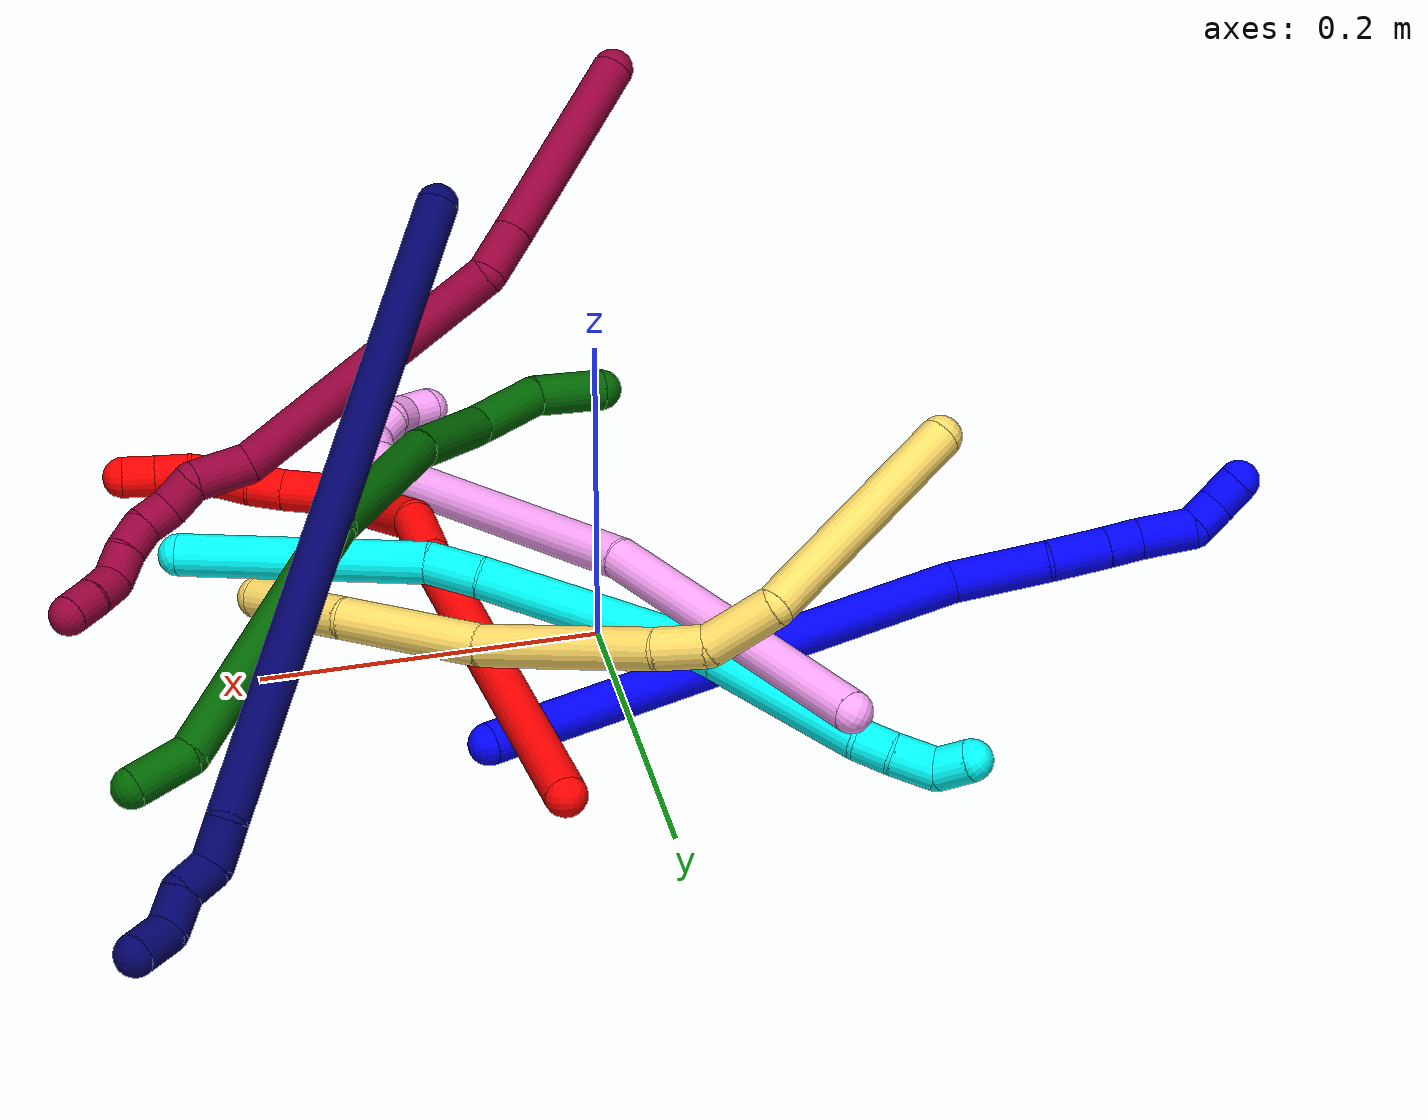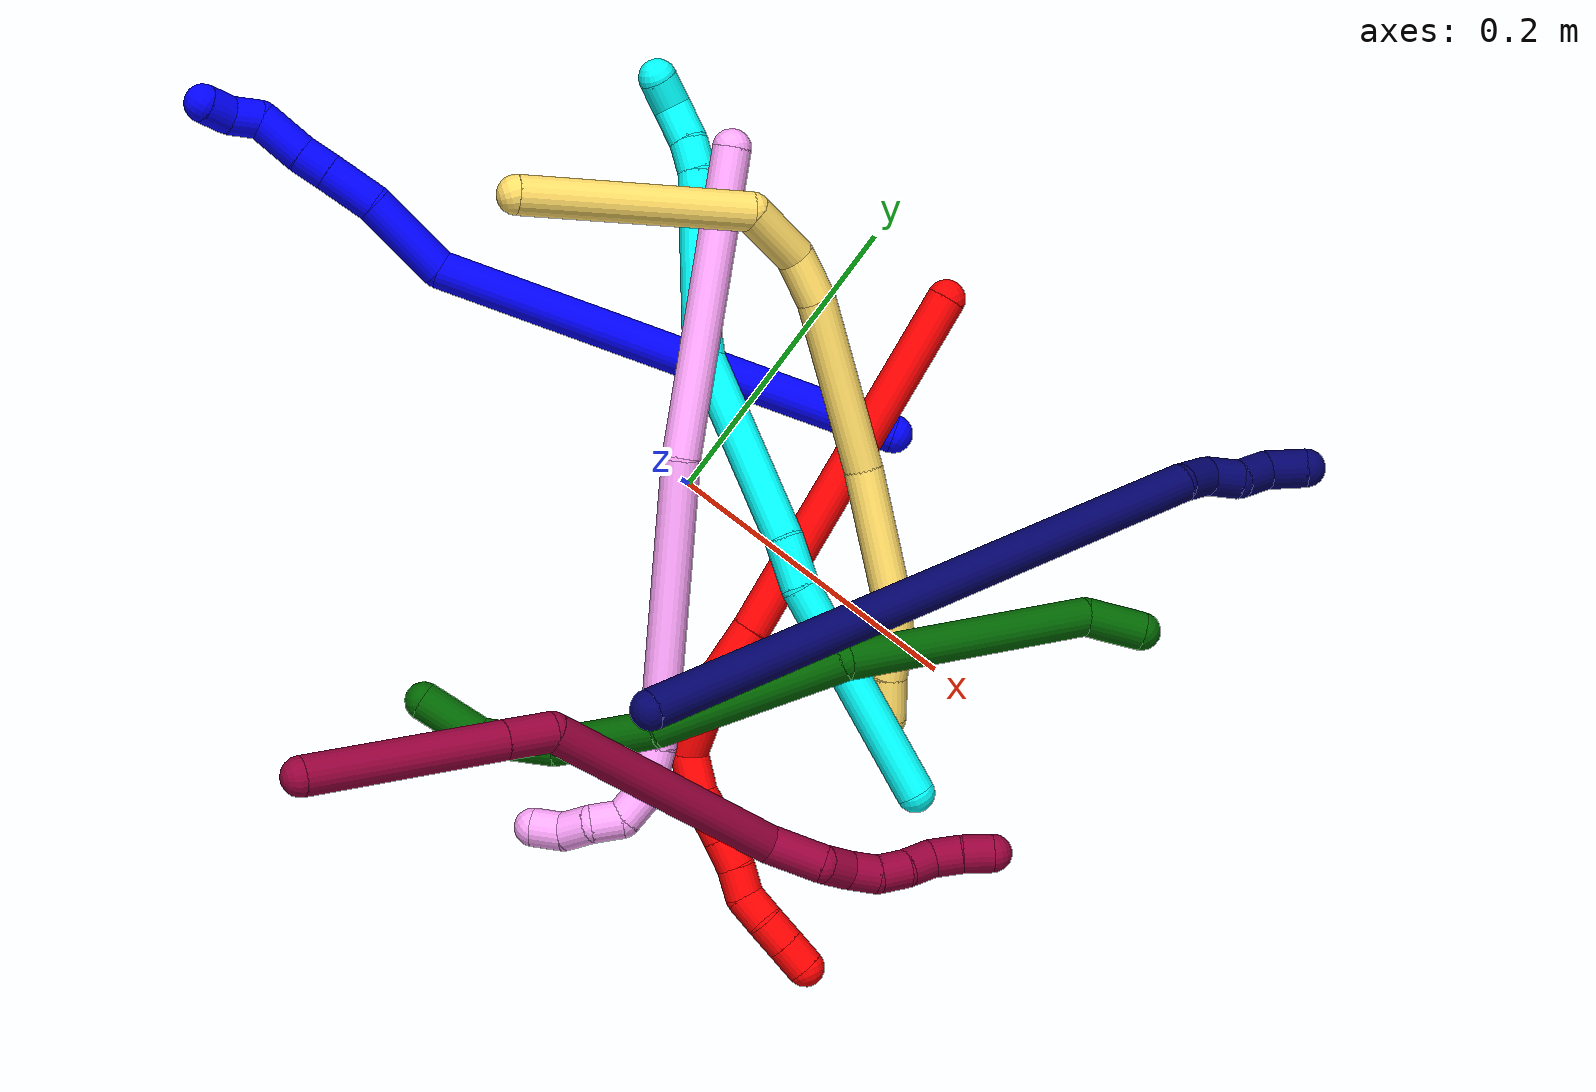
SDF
<sdf version="1.7">
 <world name="default">
  <plugin name="TubeGeneratorPlugin" filename="libtube_generator_plugin.so"/>
  <model name="photoneo_s_sensor">
   <static>1</static>
   <pose>0 0 2 1.57079 1.57079 3.14159</pose>
   <link name="link">
    <inertial><mass>0.1</mass></inertial>
    <sensor name="sensor" type="depth">
     <update_rate>30</update_rate>
     <camera>
      <horizontal_fov>1.22</horizontal_fov>
      <image><width>1920</width><height>1200</height><format>B8G8R8</format></image>
      <clip><near>0.1</near><far>4</far></clip>
      <depth_camera><output>points</output></depth_camera>
     </camera>
     <plugin name="camera_plugin" filename="libgazebo_ros_depth_camera.so">
      <baseline>0.2</baseline>
      <alwaysOn>1</alwaysOn>
      <updateRate>0.0</updateRate>
      <cameraName>camera_ir</cameraName>
      <imageTopicName>/camera/color/image_raw</imageTopicName>
      <cameraInfoTopicName>/camera/color/camera_info</cameraInfoTopicName>
      <depthImageTopicName>/camera/depth/image_raw</depthImageTopicName>
      <depthImageCameraInfoTopicName>/camera/depth/camera_info</depthImageCameraInfoTopicName>
      <pointCloudTopicName>/camera/depth/points</pointCloudTopicName>
      <frameName>fr_optical</frameName>
      <pointCloudCutoff>0.1</pointCloudCutoff>
      <pointCloudCutoffMax>2.0</pointCloudCutoffMax>
      <distortionK1>0</distortionK1>
      <distortionK2>0</distortionK2>
      <distortionK3>0</distortionK3>
      <distortionT1>0</distortionT1>
      <distortionT2>0</distortionT2>
      <CxPrime>0</CxPrime>
      <Cx>0</Cx>
      <Cy>0</Cy>
      <focalLength>0</focalLength>
      <hackBaseline>0</hackBaseline>
     </plugin>
    </sensor>
   </link>
  </model>
  <gravity>0 0 -9.8</gravity>
  <magnetic_field>6e-06 2.3e-05 -4.2e-05</magnetic_field>
  <atmosphere type="adiabatic"/>
  <physics name="default_physics" default="0" type="ode">
   <max_step_size>0.003</max_step_size>
   <real_time_factor>1</real_time_factor>
   <real_time_update_rate>1000</real_time_update_rate>
   <max_contacts>10000</max_contacts>
   <ode>
    <solver>
     <type>quick</type>
     <iters>100</iters>
     <sor>1.3</sor>
     <use_dynamic_moi_rescaling>0</use_dynamic_moi_rescaling>
    </solver>
    <constraints>
     <contact_max_correcting_vel>0</contact_max_correcting_vel>
     <contact_surface_layer>0.001</contact_surface_layer>
     <cfm>0</cfm>
     <erp>0.2</erp>
    </constraints>
   </ode>
  </physics>
  <scene><ambient>0.4 0.4 0.4 1</ambient><background>0.7 0.7 0.7 1</background><shadows>0</shadows></scene>
  <audio><device>default</device></audio>
  <spherical_coordinates>
   <surface_model>EARTH_WGS84</surface_model>
   <latitude_deg>0</latitude_deg>
   <longitude_deg>0</longitude_deg>
   <elevation>0</elevation>
   <heading_deg>0</heading_deg>
  </spherical_coordinates>
  <model name="bin">
   <static>1</static>
   <link name="bottom">
    <collision name="collision-bottom">
     <pose>0 0 -0.01 0 -0 0</pose>
     <geometry><box><size>0.8 0.6 0.02</size></box></geometry>
     <surface>
      <friction><ode><mu>100</mu><mu2>100</mu2></ode></friction>
      <contact><collide_bitmask>65535</collide_bitmask></contact>
     </surface>
    </collision>
   </link>
   <link name="west_wall">
    <collision name="collision-west_wall">
     <pose>-0.41 0 0.1 0 -0 0</pose>
     <geometry><box><size>0.02 0.6 0.2</size></box></geometry>
     <surface>
      <friction><ode><mu>100</mu><mu2>100</mu2></ode></friction>
      <contact><collide_bitmask>65535</collide_bitmask></contact>
     </surface>
    </collision>
   </link>
   <link name="east_wall">
    <collision name="collision-east_wall">
     <pose>0.41 0 0.1 0 -0 0</pose>
     <geometry><box><size>0.02 0.6 0.2</size></box></geometry>
     <surface>
      <friction><ode><mu>100</mu><mu2>100</mu2></ode></friction>
      <contact><collide_bitmask>65535</collide_bitmask></contact>
     </surface>
    </collision>
   </link>
   <link name="south_wall">
    <collision name="collision-south_wall">
     <pose>0 -0.31 0.1 0 -0 0</pose>
     <geometry><box><size>0.8 0.02 0.2</size></box></geometry>
     <surface>
      <friction><ode><mu>100</mu><mu2>100</mu2></ode></friction>
      <contact><collide_bitmask>65535</collide_bitmask></contact>
     </surface>
    </collision>
   </link>
   <link name="north_wall">
    <collision name="collision-north_wall">
     <pose>0 0.31 0.1 0 -0 0</pose>
     <geometry><box><size>0.8 0.02 0.2</size></box></geometry>
     <surface>
      <friction><ode><mu>100</mu><mu2>100</mu2></ode></friction>
      <contact><collide_bitmask>65535</collide_bitmask></contact>
     </surface>
    </collision>
   </link>
  </model>
  <model name="1">
   <static>0</static>
   <link name="1">
    <collision name="collision-cylinder-e_1_1_4">
     <pose>-0.03386 -0.010622 0.151337 0.070076 -0.21959 -0.007728</pose>
     <geometry><cylinder><radius>0.0125</radius><length>0.310884</length></cylinder></geometry>
     <surface>
      <friction><ode><mu>1.16</mu><mu2>1.16</mu2><slip1>0</slip1><slip2>0</slip2></ode></friction>
      <contact><ode><kp>1e+06</kp><kd>1</kd><max_vel>0</max_vel><min_depth>0.001</min_depth></ode></contact>
     </surface>
    </collision>
    <visual name="visual-cylinder-e_1_1_4">
     <pose>-0.03386 -0.010622 0.151337 0.070076 -0.21959 -0.007728</pose>
     <geometry><cylinder><radius>0.0125</radius><length>0.310884</length></cylinder></geometry>
     <material><ambient>0 0 1 1</ambient></material>
    </visual>
    <collision name="collision-cylinder-e_2_4_5">
     <pose>-0.06075 -0.018935 0.331298 -0.080514 0.238074 -0.009635</pose>
     <geometry><cylinder><radius>0.0125</radius><length>0.059103</length></cylinder></geometry>
     <surface>
      <friction><ode><mu>1.16</mu><mu2>1.16</mu2><slip1>0</slip1><slip2>0</slip2></ode></friction>
      <contact><ode><kp>1e+06</kp><kd>1</kd><max_vel>0</max_vel><min_depth>0.001</min_depth></ode></contact>
     </surface>
    </collision>
    <visual name="visual-cylinder-e_2_4_5">
     <pose>-0.06075 -0.018935 0.331298 -0.080514 0.238074 -0.009635</pose>
     <geometry><cylinder><radius>0.0125</radius><length>0.059103</length></cylinder></geometry>
     <material><ambient>0 0 1 1</ambient></material>
    </visual>
    <collision name="collision-cylinder-e_3_5_6">
     <pose>-0.053308 -0.015807 0.377663 -0.046092 0.026617 -0.000614</pose>
     <geometry><cylinder><radius>0.0125</radius><length>0.035529</length></cylinder></geometry>
     <surface>
      <friction><ode><mu>1.16</mu><mu2>1.16</mu2><slip1>0</slip1><slip2>0</slip2></ode></friction>
      <contact><ode><kp>1e+06</kp><kd>1</kd><max_vel>0</max_vel><min_depth>0.001</min_depth></ode></contact>
     </surface>
    </collision>
    <visual name="visual-cylinder-e_3_5_6">
     <pose>-0.053308 -0.015807 0.377663 -0.046092 0.026617 -0.000614</pose>
     <geometry><cylinder><radius>0.0125</radius><length>0.035529</length></cylinder></geometry>
     <material><ambient>0 0 1 1</ambient></material>
    </visual>
    <collision name="collision-cylinder-e_4_6_7">
     <pose>-0.052601 -0.014761 0.405688 -0.022123 0.022843 -0.000253</pose>
     <geometry><cylinder><radius>0.0125</radius><length>0.020581</length></cylinder></geometry>
     <surface>
      <friction><ode><mu>1.16</mu><mu2>1.16</mu2><slip1>0</slip1><slip2>0</slip2></ode></friction>
      <contact><ode><kp>1e+06</kp><kd>1</kd><max_vel>0</max_vel><min_depth>0.001</min_depth></ode></contact>
     </surface>
    </collision>
    <visual name="visual-cylinder-e_4_6_7">
     <pose>-0.052601 -0.014761 0.405688 -0.022123 0.022843 -0.000253</pose>
     <geometry><cylinder><radius>0.0125</radius><length>0.020581</length></cylinder></geometry>
     <material><ambient>0 0 1 1</ambient></material>
    </visual>
    <collision name="collision-cylinder-e_5_7_8">
     <pose>-0.050371 -0.01308 0.432483 -0.087859 0.119751 -0.00527</pose>
     <geometry><cylinder><radius>0.0125</radius><length>0.033388</length></cylinder></geometry>
     <surface>
      <friction><ode><mu>1.16</mu><mu2>1.16</mu2><slip1>0</slip1><slip2>0</slip2></ode></friction>
      <contact><ode><kp>1e+06</kp><kd>1</kd><max_vel>0</max_vel><min_depth>0.001</min_depth></ode></contact>
     </surface>
    </collision>
    <visual name="visual-cylinder-e_5_7_8">
     <pose>-0.050371 -0.01308 0.432483 -0.087859 0.119751 -0.00527</pose>
     <geometry><cylinder><radius>0.0125</radius><length>0.033388</length></cylinder></geometry>
     <material><ambient>0 0 1 1</ambient></material>
    </visual>
    <collision name="collision-cylinder-e_6_8_9">
     <pose>-0.049725 -0.016346 0.457891 0.487803 -0.132997 -0.033143</pose>
     <geometry><cylinder><radius>0.0125</radius><length>0.020324</length></cylinder></geometry>
     <surface>
      <friction><ode><mu>1.16</mu><mu2>1.16</mu2><slip1>0</slip1><slip2>0</slip2></ode></friction>
      <contact><ode><kp>1e+06</kp><kd>1</kd><max_vel>0</max_vel><min_depth>0.001</min_depth></ode></contact>
     </surface>
    </collision>
    <visual name="visual-cylinder-e_6_8_9">
     <pose>-0.049725 -0.016346 0.457891 0.487803 -0.132997 -0.033143</pose>
     <geometry><cylinder><radius>0.0125</radius><length>0.020324</length></cylinder></geometry>
     <material><ambient>0 0 1 1</ambient></material>
    </visual>
    <collision name="collision-cylinder-e_7_9_2">
     <pose>-0.048088 -0.026011 0.475069 0.538265 0.300073 0.083346</pose>
     <geometry><cylinder><radius>0.0125</radius><length>0.020192</length></cylinder></geometry>
     <surface>
      <friction><ode><mu>1.16</mu><mu2>1.16</mu2><slip1>0</slip1><slip2>0</slip2></ode></friction>
      <contact><ode><kp>1e+06</kp><kd>1</kd><max_vel>0</max_vel><min_depth>0.001</min_depth></ode></contact>
     </surface>
    </collision>
    <visual name="visual-cylinder-e_7_9_2">
     <pose>-0.048088 -0.026011 0.475069 0.538265 0.300073 0.083346</pose>
     <geometry><cylinder><radius>0.0125</radius><length>0.020192</length></cylinder></geometry>
     <material><ambient>0 0 1 1</ambient></material>
    </visual>
    <collision name="collision-sphere-2">
     <pose>-0.045104 -0.030955 0.48335 0 -0 0</pose>
     <geometry><sphere><radius>0.0125</radius></sphere></geometry>
     <surface>
      <friction><ode><mu>1.16</mu><mu2>1.16</mu2><slip1>0</slip1><slip2>0</slip2></ode></friction>
      <contact><ode><kp>1e+06</kp><kd>1</kd><max_vel>0</max_vel><min_depth>0.001</min_depth></ode></contact>
     </surface>
    </collision>
    <visual name="visual-sphere-2">
     <pose>-0.045104 -0.030955 0.48335 0 -0 0</pose>
     <geometry><sphere><radius>0.0125</radius></sphere></geometry>
     <material><ambient>0 0 1 1</ambient></material>
    </visual>
    <collision name="collision-sphere-9">
     <pose>-0.051072 -0.021067 0.466788 0 -0 0</pose>
     <geometry><sphere><radius>0.0125</radius></sphere></geometry>
     <surface>
      <friction><ode><mu>1.16</mu><mu2>1.16</mu2><slip1>0</slip1><slip2>0</slip2></ode></friction>
      <contact><ode><kp>1e+06</kp><kd>1</kd><max_vel>0</max_vel><min_depth>0.001</min_depth></ode></contact>
     </surface>
    </collision>
    <visual name="visual-sphere-9">
     <pose>-0.051072 -0.021067 0.466788 0 -0 0</pose>
     <geometry><sphere><radius>0.0125</radius></sphere></geometry>
     <material><ambient>0 0 1 1</ambient></material>
    </visual>
    <collision name="collision-sphere-4">
     <pose>-0.06772 -0.021245 0.302674 0 -0 0</pose>
     <geometry><sphere><radius>0.0125</radius></sphere></geometry>
     <surface>
      <friction><ode><mu>1.16</mu><mu2>1.16</mu2><slip1>0</slip1><slip2>0</slip2></ode></friction>
      <contact><ode><kp>1e+06</kp><kd>1</kd><max_vel>0</max_vel><min_depth>0.001</min_depth></ode></contact>
     </surface>
    </collision>
    <visual name="visual-sphere-4">
     <pose>-0.06772 -0.021245 0.302674 0 -0 0</pose>
     <geometry><sphere><radius>0.0125</radius></sphere></geometry>
     <material><ambient>0 0 1 1</ambient></material>
    </visual>
    <collision name="collision-sphere-1">
     <geometry><sphere><radius>0.0125</radius></sphere></geometry>
     <surface>
      <friction><ode><mu>1.16</mu><mu2>1.16</mu2><slip1>0</slip1><slip2>0</slip2></ode></friction>
      <contact><ode><kp>1e+06</kp><kd>1</kd><max_vel>0</max_vel><min_depth>0.001</min_depth></ode></contact>
     </surface>
    </collision>
    <visual name="visual-sphere-1">
     <geometry><sphere><radius>0.0125</radius></sphere></geometry>
     <material><ambient>0 0 1 1</ambient></material>
    </visual>
    <collision name="collision-sphere-8">
     <pose>-0.048377 -0.011625 0.448993 0 -0 0</pose>
     <geometry><sphere><radius>0.0125</radius></sphere></geometry>
     <surface>
      <friction><ode><mu>1.16</mu><mu2>1.16</mu2><slip1>0</slip1><slip2>0</slip2></ode></friction>
      <contact><ode><kp>1e+06</kp><kd>1</kd><max_vel>0</max_vel><min_depth>0.001</min_depth></ode></contact>
     </surface>
    </collision>
    <visual name="visual-sphere-8">
     <pose>-0.048377 -0.011625 0.448993 0 -0 0</pose>
     <geometry><sphere><radius>0.0125</radius></sphere></geometry>
     <material><ambient>0 0 1 1</ambient></material>
    </visual>
    <collision name="collision-sphere-5">
     <pose>-0.053781 -0.016626 0.359923 0 -0 0</pose>
     <geometry><sphere><radius>0.0125</radius></sphere></geometry>
     <surface>
      <friction><ode><mu>1.16</mu><mu2>1.16</mu2><slip1>0</slip1><slip2>0</slip2></ode></friction>
      <contact><ode><kp>1e+06</kp><kd>1</kd><max_vel>0</max_vel><min_depth>0.001</min_depth></ode></contact>
     </surface>
    </collision>
    <visual name="visual-sphere-5">
     <pose>-0.053781 -0.016626 0.359923 0 -0 0</pose>
     <geometry><sphere><radius>0.0125</radius></sphere></geometry>
     <material><ambient>0 0 1 1</ambient></material>
    </visual>
    <collision name="collision-sphere-6">
     <pose>-0.052836 -0.014989 0.395402 0 -0 0</pose>
     <geometry><sphere><radius>0.0125</radius></sphere></geometry>
     <surface>
      <friction><ode><mu>1.16</mu><mu2>1.16</mu2><slip1>0</slip1><slip2>0</slip2></ode></friction>
      <contact><ode><kp>1e+06</kp><kd>1</kd><max_vel>0</max_vel><min_depth>0.001</min_depth></ode></contact>
     </surface>
    </collision>
    <visual name="visual-sphere-6">
     <pose>-0.052836 -0.014989 0.395402 0 -0 0</pose>
     <geometry><sphere><radius>0.0125</radius></sphere></geometry>
     <material><ambient>0 0 1 1</ambient></material>
    </visual>
    <collision name="collision-sphere-7">
     <pose>-0.052366 -0.014534 0.415973 0 -0 0</pose>
     <geometry><sphere><radius>0.0125</radius></sphere></geometry>
     <surface>
      <friction><ode><mu>1.16</mu><mu2>1.16</mu2><slip1>0</slip1><slip2>0</slip2></ode></friction>
      <contact><ode><kp>1e+06</kp><kd>1</kd><max_vel>0</max_vel><min_depth>0.001</min_depth></ode></contact>
     </surface>
    </collision>
    <visual name="visual-sphere-7">
     <pose>-0.052366 -0.014534 0.415973 0 -0 0</pose>
     <geometry><sphere><radius>0.0125</radius></sphere></geometry>
     <material><ambient>0 0 1 1</ambient></material>
    </visual>
    <inertial>
     <pose>-0.041514 -0.013162 0.243469 0 -0 0</pose>
     <mass>0.5</mass>
     <inertia>
      <ixx>0.002466</ixx>
      <ixy>0</ixy>
      <ixz>0</ixz>
      <iyy>0.002522</iyy>
      <iyz>0</iyz>
      <izz>0.000751</izz>
     </inertia>
    </inertial>
   </link>
   <pose>0.086418 0.105026 0.011497 -1.43264 -0.747129 1.56791</pose>
  </model>
  <model name="2">
   <static>0</static>
   <link name="2">
    <collision name="collision-cylinder-e_1_1_4">
     <pose>0.00181 -0.098809 0.072326 0.938934 0.014782 0.007499</pose>
     <geometry><cylinder><radius>0.0125</radius><length>0.244929</length></cylinder></geometry>
     <surface>
      <friction><ode><mu>1.16</mu><mu2>1.16</mu2><slip1>0</slip1><slip2>0</slip2></ode></friction>
      <contact><ode><kp>1e+06</kp><kd>1</kd><max_vel>0</max_vel><min_depth>0.001</min_depth></ode></contact>
     </surface>
    </collision>
    <visual name="visual-cylinder-e_1_1_4">
     <pose>0.00181 -0.098809 0.072326 0.938934 0.014782 0.007499</pose>
     <geometry><cylinder><radius>0.0125</radius><length>0.244929</length></cylinder></geometry>
     <material><ambient>1 0 0 1</ambient></material>
    </visual>
    <collision name="collision-cylinder-e_2_4_5">
     <pose>0.004131 -0.214495 0.155416 1.00301 0.025502 0.013982</pose>
     <geometry><cylinder><radius>0.0125</radius><length>0.040048</length></cylinder></geometry>
     <surface>
      <friction><ode><mu>1.16</mu><mu2>1.16</mu2><slip1>0</slip1><slip2>0</slip2></ode></friction>
      <contact><ode><kp>1e+06</kp><kd>1</kd><max_vel>0</max_vel><min_depth>0.001</min_depth></ode></contact>
     </surface>
    </collision>
    <visual name="visual-cylinder-e_2_4_5">
     <pose>0.004131 -0.214495 0.155416 1.00301 0.025502 0.013982</pose>
     <geometry><cylinder><radius>0.0125</radius><length>0.040048</length></cylinder></geometry>
     <material><ambient>1 0 0 1</ambient></material>
    </visual>
    <collision name="collision-cylinder-e_3_5_6">
     <pose>0.015367 -0.247654 0.185288 0.705736 0.403757 0.150465</pose>
     <geometry><cylinder><radius>0.0125</radius><length>0.054598</length></cylinder></geometry>
     <surface>
      <friction><ode><mu>1.16</mu><mu2>1.16</mu2><slip1>0</slip1><slip2>0</slip2></ode></friction>
      <contact><ode><kp>1e+06</kp><kd>1</kd><max_vel>0</max_vel><min_depth>0.001</min_depth></ode></contact>
     </surface>
    </collision>
    <visual name="visual-cylinder-e_3_5_6">
     <pose>0.015367 -0.247654 0.185288 0.705736 0.403757 0.150465</pose>
     <geometry><cylinder><radius>0.0125</radius><length>0.054598</length></cylinder></geometry>
     <material><ambient>1 0 0 1</ambient></material>
    </visual>
    <collision name="collision-cylinder-e_4_6_7">
     <pose>0.023814 -0.266351 0.21722 0.186079 -0.172844 -0.016168</pose>
     <geometry><cylinder><radius>0.0125</radius><length>0.026495</length></cylinder></geometry>
     <surface>
      <friction><ode><mu>1.16</mu><mu2>1.16</mu2><slip1>0</slip1><slip2>0</slip2></ode></friction>
      <contact><ode><kp>1e+06</kp><kd>1</kd><max_vel>0</max_vel><min_depth>0.001</min_depth></ode></contact>
     </surface>
    </collision>
    <visual name="visual-cylinder-e_4_6_7">
     <pose>0.023814 -0.266351 0.21722 0.186079 -0.172844 -0.016168</pose>
     <geometry><cylinder><radius>0.0125</radius><length>0.026495</length></cylinder></geometry>
     <material><ambient>1 0 0 1</ambient></material>
    </visual>
    <collision name="collision-cylinder-e_5_7_8">
     <pose>0.020434 -0.26765 0.246345 -0.068286 -0.067302 0.0023</pose>
     <geometry><cylinder><radius>0.0125</radius><length>0.032749</length></cylinder></geometry>
     <surface>
      <friction><ode><mu>1.16</mu><mu2>1.16</mu2><slip1>0</slip1><slip2>0</slip2></ode></friction>
      <contact><ode><kp>1e+06</kp><kd>1</kd><max_vel>0</max_vel><min_depth>0.001</min_depth></ode></contact>
     </surface>
    </collision>
    <visual name="visual-cylinder-e_5_7_8">
     <pose>0.020434 -0.26765 0.246345 -0.068286 -0.067302 0.0023</pose>
     <geometry><cylinder><radius>0.0125</radius><length>0.032749</length></cylinder></geometry>
     <material><ambient>1 0 0 1</ambient></material>
    </visual>
    <collision name="collision-cylinder-e_6_8_9">
     <pose>0.018225 -0.266083 0.272897 -0.044145 -0.107483 0.002375</pose>
     <geometry><cylinder><radius>0.0125</radius><length>0.020645</length></cylinder></geometry>
     <surface>
      <friction><ode><mu>1.16</mu><mu2>1.16</mu2><slip1>0</slip1><slip2>0</slip2></ode></friction>
      <contact><ode><kp>1e+06</kp><kd>1</kd><max_vel>0</max_vel><min_depth>0.001</min_depth></ode></contact>
     </surface>
    </collision>
    <visual name="visual-cylinder-e_6_8_9">
     <pose>0.018225 -0.266083 0.272897 -0.044145 -0.107483 0.002375</pose>
     <geometry><cylinder><radius>0.0125</radius><length>0.020645</length></cylinder></geometry>
     <material><ambient>1 0 0 1</ambient></material>
    </visual>
    <collision name="collision-cylinder-e_7_9_10">
     <pose>0.016321 -0.266932 0.293205 0.128845 -0.078406 -0.005061</pose>
     <geometry><cylinder><radius>0.0125</radius><length>0.020342</length></cylinder></geometry>
     <surface>
      <friction><ode><mu>1.16</mu><mu2>1.16</mu2><slip1>0</slip1><slip2>0</slip2></ode></friction>
      <contact><ode><kp>1e+06</kp><kd>1</kd><max_vel>0</max_vel><min_depth>0.001</min_depth></ode></contact>
     </surface>
    </collision>
    <visual name="visual-cylinder-e_7_9_10">
     <pose>0.016321 -0.266932 0.293205 0.128845 -0.078406 -0.005061</pose>
     <geometry><cylinder><radius>0.0125</radius><length>0.020342</length></cylinder></geometry>
     <material><ambient>1 0 0 1</ambient></material>
    </visual>
    <collision name="collision-cylinder-e_8_10_11">
     <pose>0.012773 -0.265425 0.312551 -0.293783 -0.276233 0.041127</pose>
     <geometry><cylinder><radius>0.0125</radius><length>0.020177</length></cylinder></geometry>
     <surface>
      <friction><ode><mu>1.16</mu><mu2>1.16</mu2><slip1>0</slip1><slip2>0</slip2></ode></friction>
      <contact><ode><kp>1e+06</kp><kd>1</kd><max_vel>0</max_vel><min_depth>0.001</min_depth></ode></contact>
     </surface>
    </collision>
    <visual name="visual-cylinder-e_8_10_11">
     <pose>0.012773 -0.265425 0.312551 -0.293783 -0.276233 0.041127</pose>
     <geometry><cylinder><radius>0.0125</radius><length>0.020177</length></cylinder></geometry>
     <material><ambient>1 0 0 1</ambient></material>
    </visual>
    <collision name="collision-cylinder-e_9_11_12">
     <pose>0.009394 -0.259607 0.331363 -0.305923 -0.062779 0.009681</pose>
     <geometry><cylinder><radius>0.0125</radius><length>0.020011</length></cylinder></geometry>
     <surface>
      <friction><ode><mu>1.16</mu><mu2>1.16</mu2><slip1>0</slip1><slip2>0</slip2></ode></friction>
      <contact><ode><kp>1e+06</kp><kd>1</kd><max_vel>0</max_vel><min_depth>0.001</min_depth></ode></contact>
     </surface>
    </collision>
    <visual name="visual-cylinder-e_9_11_12">
     <pose>0.009394 -0.259607 0.331363 -0.305923 -0.062779 0.009681</pose>
     <geometry><cylinder><radius>0.0125</radius><length>0.020011</length></cylinder></geometry>
     <material><ambient>1 0 0 1</ambient></material>
    </visual>
    <collision name="collision-cylinder-e_10_12_2">
     <pose>0.007921 -0.2536 0.350391 -0.305597 -0.084631 0.013041</pose>
     <geometry><cylinder><radius>0.0125</radius><length>0.020007</length></cylinder></geometry>
     <surface>
      <friction><ode><mu>1.16</mu><mu2>1.16</mu2><slip1>0</slip1><slip2>0</slip2></ode></friction>
      <contact><ode><kp>1e+06</kp><kd>1</kd><max_vel>0</max_vel><min_depth>0.001</min_depth></ode></contact>
     </surface>
    </collision>
    <visual name="visual-cylinder-e_10_12_2">
     <pose>0.007921 -0.2536 0.350391 -0.305597 -0.084631 0.013041</pose>
     <geometry><cylinder><radius>0.0125</radius><length>0.020007</length></cylinder></geometry>
     <material><ambient>1 0 0 1</ambient></material>
    </visual>
    <collision name="collision-sphere-2">
     <pose>0.007075 -0.250601 0.359897 0 -0 0</pose>
     <geometry><sphere><radius>0.0125</radius></sphere></geometry>
     <surface>
      <friction><ode><mu>1.16</mu><mu2>1.16</mu2><slip1>0</slip1><slip2>0</slip2></ode></friction>
      <contact><ode><kp>1e+06</kp><kd>1</kd><max_vel>0</max_vel><min_depth>0.001</min_depth></ode></contact>
     </surface>
    </collision>
    <visual name="visual-sphere-2">
     <pose>0.007075 -0.250601 0.359897 0 -0 0</pose>
     <geometry><sphere><radius>0.0125</radius></sphere></geometry>
     <material><ambient>1 0 0 1</ambient></material>
    </visual>
    <collision name="collision-sphere-12">
     <pose>0.008766 -0.256599 0.340885 0 -0 0</pose>
     <geometry><sphere><radius>0.0125</radius></sphere></geometry>
     <surface>
      <friction><ode><mu>1.16</mu><mu2>1.16</mu2><slip1>0</slip1><slip2>0</slip2></ode></friction>
      <contact><ode><kp>1e+06</kp><kd>1</kd><max_vel>0</max_vel><min_depth>0.001</min_depth></ode></contact>
     </surface>
    </collision>
    <visual name="visual-sphere-12">
     <pose>0.008766 -0.256599 0.340885 0 -0 0</pose>
     <geometry><sphere><radius>0.0125</radius></sphere></geometry>
     <material><ambient>1 0 0 1</ambient></material>
    </visual>
    <collision name="collision-sphere-11">
     <pose>0.010022 -0.262614 0.321841 0 -0 0</pose>
     <geometry><sphere><radius>0.0125</radius></sphere></geometry>
     <surface>
      <friction><ode><mu>1.16</mu><mu2>1.16</mu2><slip1>0</slip1><slip2>0</slip2></ode></friction>
      <contact><ode><kp>1e+06</kp><kd>1</kd><max_vel>0</max_vel><min_depth>0.001</min_depth></ode></contact>
     </surface>
    </collision>
    <visual name="visual-sphere-11">
     <pose>0.010022 -0.262614 0.321841 0 -0 0</pose>
     <geometry><sphere><radius>0.0125</radius></sphere></geometry>
     <material><ambient>1 0 0 1</ambient></material>
    </visual>
    <collision name="collision-sphere-10">
     <pose>0.015525 -0.268235 0.303261 0 -0 0</pose>
     <geometry><sphere><radius>0.0125</radius></sphere></geometry>
     <surface>
      <friction><ode><mu>1.16</mu><mu2>1.16</mu2><slip1>0</slip1><slip2>0</slip2></ode></friction>
      <contact><ode><kp>1e+06</kp><kd>1</kd><max_vel>0</max_vel><min_depth>0.001</min_depth></ode></contact>
     </surface>
    </collision>
    <visual name="visual-sphere-10">
     <pose>0.015525 -0.268235 0.303261 0 -0 0</pose>
     <geometry><sphere><radius>0.0125</radius></sphere></geometry>
     <material><ambient>1 0 0 1</ambient></material>
    </visual>
    <collision name="collision-sphere-9">
     <pose>0.017118 -0.26563 0.28315 0 -0 0</pose>
     <geometry><sphere><radius>0.0125</radius></sphere></geometry>
     <surface>
      <friction><ode><mu>1.16</mu><mu2>1.16</mu2><slip1>0</slip1><slip2>0</slip2></ode></friction>
      <contact><ode><kp>1e+06</kp><kd>1</kd><max_vel>0</max_vel><min_depth>0.001</min_depth></ode></contact>
     </surface>
    </collision>
    <visual name="visual-sphere-9">
     <pose>0.017118 -0.26563 0.28315 0 -0 0</pose>
     <geometry><sphere><radius>0.0125</radius></sphere></geometry>
     <material><ambient>1 0 0 1</ambient></material>
    </visual>
    <collision name="collision-sphere-4">
     <pose>0.00362 -0.197619 0.144651 0 -0 0</pose>
     <geometry><sphere><radius>0.0125</radius></sphere></geometry>
     <surface>
      <friction><ode><mu>1.16</mu><mu2>1.16</mu2><slip1>0</slip1><slip2>0</slip2></ode></friction>
      <contact><ode><kp>1e+06</kp><kd>1</kd><max_vel>0</max_vel><min_depth>0.001</min_depth></ode></contact>
     </surface>
    </collision>
    <visual name="visual-sphere-4">
     <pose>0.00362 -0.197619 0.144651 0 -0 0</pose>
     <geometry><sphere><radius>0.0125</radius></sphere></geometry>
     <material><ambient>1 0 0 1</ambient></material>
    </visual>
    <collision name="collision-sphere-1">
     <geometry><sphere><radius>0.0125</radius></sphere></geometry>
     <surface>
      <friction><ode><mu>1.16</mu><mu2>1.16</mu2><slip1>0</slip1><slip2>0</slip2></ode></friction>
      <contact><ode><kp>1e+06</kp><kd>1</kd><max_vel>0</max_vel><min_depth>0.001</min_depth></ode></contact>
     </surface>
    </collision>
    <visual name="visual-sphere-1">
     <geometry><sphere><radius>0.0125</radius></sphere></geometry>
     <material><ambient>1 0 0 1</ambient></material>
    </visual>
    <collision name="collision-sphere-8">
     <pose>0.019333 -0.266535 0.262644 0 -0 0</pose>
     <geometry><sphere><radius>0.0125</radius></sphere></geometry>
     <surface>
      <friction><ode><mu>1.16</mu><mu2>1.16</mu2><slip1>0</slip1><slip2>0</slip2></ode></friction>
      <contact><ode><kp>1e+06</kp><kd>1</kd><max_vel>0</max_vel><min_depth>0.001</min_depth></ode></contact>
     </surface>
    </collision>
    <visual name="visual-sphere-8">
     <pose>0.019333 -0.266535 0.262644 0 -0 0</pose>
     <geometry><sphere><radius>0.0125</radius></sphere></geometry>
     <material><ambient>1 0 0 1</ambient></material>
    </visual>
    <collision name="collision-sphere-5">
     <pose>0.004642 -0.231372 0.16618 0 -0 0</pose>
     <geometry><sphere><radius>0.0125</radius></sphere></geometry>
     <surface>
      <friction><ode><mu>1.16</mu><mu2>1.16</mu2><slip1>0</slip1><slip2>0</slip2></ode></friction>
      <contact><ode><kp>1e+06</kp><kd>1</kd><max_vel>0</max_vel><min_depth>0.001</min_depth></ode></contact>
     </surface>
    </collision>
    <visual name="visual-sphere-5">
     <pose>0.004642 -0.231372 0.16618 0 -0 0</pose>
     <geometry><sphere><radius>0.0125</radius></sphere></geometry>
     <material><ambient>1 0 0 1</ambient></material>
    </visual>
    <collision name="collision-sphere-6">
     <pose>0.026092 -0.263936 0.204395 0 -0 0</pose>
     <geometry><sphere><radius>0.0125</radius></sphere></geometry>
     <surface>
      <friction><ode><mu>1.16</mu><mu2>1.16</mu2><slip1>0</slip1><slip2>0</slip2></ode></friction>
      <contact><ode><kp>1e+06</kp><kd>1</kd><max_vel>0</max_vel><min_depth>0.001</min_depth></ode></contact>
     </surface>
    </collision>
    <visual name="visual-sphere-6">
     <pose>0.026092 -0.263936 0.204395 0 -0 0</pose>
     <geometry><sphere><radius>0.0125</radius></sphere></geometry>
     <material><ambient>1 0 0 1</ambient></material>
    </visual>
    <collision name="collision-sphere-7">
     <pose>0.021535 -0.268765 0.230045 0 -0 0</pose>
     <geometry><sphere><radius>0.0125</radius></sphere></geometry>
     <surface>
      <friction><ode><mu>1.16</mu><mu2>1.16</mu2><slip1>0</slip1><slip2>0</slip2></ode></friction>
      <contact><ode><kp>1e+06</kp><kd>1</kd><max_vel>0</max_vel><min_depth>0.001</min_depth></ode></contact>
     </surface>
    </collision>
    <visual name="visual-sphere-7">
     <pose>0.021535 -0.268765 0.230045 0 -0 0</pose>
     <geometry><sphere><radius>0.0125</radius></sphere></geometry>
     <material><ambient>1 0 0 1</ambient></material>
    </visual>
    <inertial>
     <pose>0.008121 -0.177364 0.158847 0 -0 0</pose>
     <mass>0.5</mass>
     <inertia>
      <ixx>0.001281</ixx>
      <ixy>0</ixy>
      <ixz>0</ixz>
      <iyy>0.000751</iyy>
      <iyz>0</iyz>
      <izz>0.001015</izz>
     </inertia>
    </inertial>
   </link>
   <pose>0.061166 0.192837 0.036157 -2.45289 1.4407 -2.97043</pose>
  </model>
  <model name="3">
   <static>0</static>
   <link name="3">
    <collision name="collision-cylinder-e_1_1_4">
     <pose>-0.036041 0.010094 0.065071 -0.153904 -0.500792 0.039436</pose>
     <geometry><cylinder><radius>0.0125</radius><length>0.150135</length></cylinder></geometry>
     <surface>
      <friction><ode><mu>1.16</mu><mu2>1.16</mu2><slip1>0</slip1><slip2>0</slip2></ode></friction>
      <contact><ode><kp>1e+06</kp><kd>1</kd><max_vel>0</max_vel><min_depth>0.001</min_depth></ode></contact>
     </surface>
    </collision>
    <visual name="visual-cylinder-e_1_1_4">
     <pose>-0.036041 0.010094 0.065071 -0.153904 -0.500792 0.039436</pose>
     <geometry><cylinder><radius>0.0125</radius><length>0.150135</length></cylinder></geometry>
     <material><ambient>0.003922 1 0.996078 1</ambient></material>
    </visual>
    <collision name="collision-cylinder-e_2_4_5">
     <pose>-0.080492 0.025983 0.142916 -0.425794 -0.54004 0.119522</pose>
     <geometry><cylinder><radius>0.0125</radius><length>0.032709</length></cylinder></geometry>
     <surface>
      <friction><ode><mu>1.16</mu><mu2>1.16</mu2><slip1>0</slip1><slip2>0</slip2></ode></friction>
      <contact><ode><kp>1e+06</kp><kd>1</kd><max_vel>0</max_vel><min_depth>0.001</min_depth></ode></contact>
     </surface>
    </collision>
    <visual name="visual-cylinder-e_2_4_5">
     <pose>-0.080492 0.025983 0.142916 -0.425794 -0.54004 0.119522</pose>
     <geometry><cylinder><radius>0.0125</radius><length>0.032709</length></cylinder></geometry>
     <material><ambient>0.003922 1 0.996078 1</ambient></material>
    </visual>
    <collision name="collision-cylinder-e_3_5_6">
     <pose>-0.128663 0.051828 0.200346 -0.422039 -0.682192 0.151784</pose>
     <geometry><cylinder><radius>0.0125</radius><length>0.12613</length></cylinder></geometry>
     <surface>
      <friction><ode><mu>1.16</mu><mu2>1.16</mu2><slip1>0</slip1><slip2>0</slip2></ode></friction>
      <contact><ode><kp>1e+06</kp><kd>1</kd><max_vel>0</max_vel><min_depth>0.001</min_depth></ode></contact>
     </surface>
    </collision>
    <visual name="visual-cylinder-e_3_5_6">
     <pose>-0.128663 0.051828 0.200346 -0.422039 -0.682192 0.151784</pose>
     <geometry><cylinder><radius>0.0125</radius><length>0.12613</length></cylinder></geometry>
     <material><ambient>0.003922 1 0.996078 1</ambient></material>
    </visual>
    <collision name="collision-cylinder-e_4_6_7">
     <pose>-0.17372 0.077333 0.252049 -0.658646 -0.536154 0.187211</pose>
     <geometry><cylinder><radius>0.0125</radius><length>0.020732</length></cylinder></geometry>
     <surface>
      <friction><ode><mu>1.16</mu><mu2>1.16</mu2><slip1>0</slip1><slip2>0</slip2></ode></friction>
      <contact><ode><kp>1e+06</kp><kd>1</kd><max_vel>0</max_vel><min_depth>0.001</min_depth></ode></contact>
     </surface>
    </collision>
    <visual name="visual-cylinder-e_4_6_7">
     <pose>-0.17372 0.077333 0.252049 -0.658646 -0.536154 0.187211</pose>
     <geometry><cylinder><radius>0.0125</radius><length>0.020732</length></cylinder></geometry>
     <material><ambient>0.003922 1 0.996078 1</ambient></material>
    </visual>
    <collision name="collision-cylinder-e_5_7_8">
     <pose>-0.198275 0.113475 0.294295 -0.717033 -0.39117 0.148202</pose>
     <geometry><cylinder><radius>0.0125</radius><length>0.101028</length></cylinder></geometry>
     <surface>
      <friction><ode><mu>1.16</mu><mu2>1.16</mu2><slip1>0</slip1><slip2>0</slip2></ode></friction>
      <contact><ode><kp>1e+06</kp><kd>1</kd><max_vel>0</max_vel><min_depth>0.001</min_depth></ode></contact>
     </surface>
    </collision>
    <visual name="visual-cylinder-e_5_7_8">
     <pose>-0.198275 0.113475 0.294295 -0.717033 -0.39117 0.148202</pose>
     <geometry><cylinder><radius>0.0125</radius><length>0.101028</length></cylinder></geometry>
     <material><ambient>0.003922 1 0.996078 1</ambient></material>
    </visual>
    <collision name="collision-cylinder-e_6_8_9">
     <pose>-0.223383 0.148725 0.336873 -0.553829 -0.593199 0.173286</pose>
     <geometry><cylinder><radius>0.0125</radius><length>0.020924</length></cylinder></geometry>
     <surface>
      <friction><ode><mu>1.16</mu><mu2>1.16</mu2><slip1>0</slip1><slip2>0</slip2></ode></friction>
      <contact><ode><kp>1e+06</kp><kd>1</kd><max_vel>0</max_vel><min_depth>0.001</min_depth></ode></contact>
     </surface>
    </collision>
    <visual name="visual-cylinder-e_6_8_9">
     <pose>-0.223383 0.148725 0.336873 -0.553829 -0.593199 0.173286</pose>
     <geometry><cylinder><radius>0.0125</radius><length>0.020924</length></cylinder></geometry>
     <material><ambient>0.003922 1 0.996078 1</ambient></material>
    </visual>
    <collision name="collision-cylinder-e_7_9_10">
     <pose>-0.238259 0.157339 0.353023 -0.432673 -0.751416 0.172946</pose>
     <geometry><cylinder><radius>0.0125</radius><length>0.026448</length></cylinder></geometry>
     <surface>
      <friction><ode><mu>1.16</mu><mu2>1.16</mu2><slip1>0</slip1><slip2>0</slip2></ode></friction>
      <contact><ode><kp>1e+06</kp><kd>1</kd><max_vel>0</max_vel><min_depth>0.001</min_depth></ode></contact>
     </surface>
    </collision>
    <visual name="visual-cylinder-e_7_9_10">
     <pose>-0.238259 0.157339 0.353023 -0.432673 -0.751416 0.172946</pose>
     <geometry><cylinder><radius>0.0125</radius><length>0.026448</length></cylinder></geometry>
     <material><ambient>0.003922 1 0.996078 1</ambient></material>
    </visual>
    <collision name="collision-cylinder-e_8_10_2">
     <pose>-0.248943 0.161688 0.372613 -0.027454 -0.151905 0.002089</pose>
     <geometry><cylinder><radius>0.0125</radius><length>0.021895</length></cylinder></geometry>
     <surface>
      <friction><ode><mu>1.16</mu><mu2>1.16</mu2><slip1>0</slip1><slip2>0</slip2></ode></friction>
      <contact><ode><kp>1e+06</kp><kd>1</kd><max_vel>0</max_vel><min_depth>0.001</min_depth></ode></contact>
     </surface>
    </collision>
    <visual name="visual-cylinder-e_8_10_2">
     <pose>-0.248943 0.161688 0.372613 -0.027454 -0.151905 0.002089</pose>
     <geometry><cylinder><radius>0.0125</radius><length>0.021895</length></cylinder></geometry>
     <material><ambient>0.003922 1 0.996078 1</ambient></material>
    </visual>
    <collision name="collision-sphere-2">
     <pose>-0.2506 0.161985 0.383431 0 -0 0</pose>
     <geometry><sphere><radius>0.0125</radius></sphere></geometry>
     <surface>
      <friction><ode><mu>1.16</mu><mu2>1.16</mu2><slip1>0</slip1><slip2>0</slip2></ode></friction>
      <contact><ode><kp>1e+06</kp><kd>1</kd><max_vel>0</max_vel><min_depth>0.001</min_depth></ode></contact>
     </surface>
    </collision>
    <visual name="visual-sphere-2">
     <pose>-0.2506 0.161985 0.383431 0 -0 0</pose>
     <geometry><sphere><radius>0.0125</radius></sphere></geometry>
     <material><ambient>0.003922 1 0.996078 1</ambient></material>
    </visual>
    <collision name="collision-sphere-10">
     <pose>-0.247286 0.161391 0.361796 0 -0 0</pose>
     <geometry><sphere><radius>0.0125</radius></sphere></geometry>
     <surface>
      <friction><ode><mu>1.16</mu><mu2>1.16</mu2><slip1>0</slip1><slip2>0</slip2></ode></friction>
      <contact><ode><kp>1e+06</kp><kd>1</kd><max_vel>0</max_vel><min_depth>0.001</min_depth></ode></contact>
     </surface>
    </collision>
    <visual name="visual-sphere-10">
     <pose>-0.247286 0.161391 0.361796 0 -0 0</pose>
     <geometry><sphere><radius>0.0125</radius></sphere></geometry>
     <material><ambient>0.003922 1 0.996078 1</ambient></material>
    </visual>
    <collision name="collision-sphere-9">
     <pose>-0.229231 0.153288 0.34425 0 -0 0</pose>
     <geometry><sphere><radius>0.0125</radius></sphere></geometry>
     <surface>
      <friction><ode><mu>1.16</mu><mu2>1.16</mu2><slip1>0</slip1><slip2>0</slip2></ode></friction>
      <contact><ode><kp>1e+06</kp><kd>1</kd><max_vel>0</max_vel><min_depth>0.001</min_depth></ode></contact>
     </surface>
    </collision>
    <visual name="visual-sphere-9">
     <pose>-0.229231 0.153288 0.34425 0 -0 0</pose>
     <geometry><sphere><radius>0.0125</radius></sphere></geometry>
     <material><ambient>0.003922 1 0.996078 1</ambient></material>
    </visual>
    <collision name="collision-sphere-4">
     <pose>-0.072083 0.020189 0.130142 0 -0 0</pose>
     <geometry><sphere><radius>0.0125</radius></sphere></geometry>
     <surface>
      <friction><ode><mu>1.16</mu><mu2>1.16</mu2><slip1>0</slip1><slip2>0</slip2></ode></friction>
      <contact><ode><kp>1e+06</kp><kd>1</kd><max_vel>0</max_vel><min_depth>0.001</min_depth></ode></contact>
     </surface>
    </collision>
    <visual name="visual-sphere-4">
     <pose>-0.072083 0.020189 0.130142 0 -0 0</pose>
     <geometry><sphere><radius>0.0125</radius></sphere></geometry>
     <material><ambient>0.003922 1 0.996078 1</ambient></material>
    </visual>
    <collision name="collision-sphere-1">
     <geometry><sphere><radius>0.0125</radius></sphere></geometry>
     <surface>
      <friction><ode><mu>1.16</mu><mu2>1.16</mu2><slip1>0</slip1><slip2>0</slip2></ode></friction>
      <contact><ode><kp>1e+06</kp><kd>1</kd><max_vel>0</max_vel><min_depth>0.001</min_depth></ode></contact>
     </surface>
    </collision>
    <visual name="visual-sphere-1">
     <geometry><sphere><radius>0.0125</radius></sphere></geometry>
     <material><ambient>0.003922 1 0.996078 1</ambient></material>
    </visual>
    <collision name="collision-sphere-8">
     <pose>-0.217534 0.144163 0.329495 0 -0 0</pose>
     <geometry><sphere><radius>0.0125</radius></sphere></geometry>
     <surface>
      <friction><ode><mu>1.16</mu><mu2>1.16</mu2><slip1>0</slip1><slip2>0</slip2></ode></friction>
      <contact><ode><kp>1e+06</kp><kd>1</kd><max_vel>0</max_vel><min_depth>0.001</min_depth></ode></contact>
     </surface>
    </collision>
    <visual name="visual-sphere-8">
     <pose>-0.217534 0.144163 0.329495 0 -0 0</pose>
     <geometry><sphere><radius>0.0125</radius></sphere></geometry>
     <material><ambient>0.003922 1 0.996078 1</ambient></material>
    </visual>
    <collision name="collision-sphere-5">
     <pose>-0.088901 0.031777 0.155691 0 -0 0</pose>
     <geometry><sphere><radius>0.0125</radius></sphere></geometry>
     <surface>
      <friction><ode><mu>1.16</mu><mu2>1.16</mu2><slip1>0</slip1><slip2>0</slip2></ode></friction>
      <contact><ode><kp>1e+06</kp><kd>1</kd><max_vel>0</max_vel><min_depth>0.001</min_depth></ode></contact>
     </surface>
    </collision>
    <visual name="visual-sphere-5">
     <pose>-0.088901 0.031777 0.155691 0 -0 0</pose>
     <geometry><sphere><radius>0.0125</radius></sphere></geometry>
     <material><ambient>0.003922 1 0.996078 1</ambient></material>
    </visual>
    <collision name="collision-sphere-6">
     <pose>-0.168425 0.071879 0.245002 0 -0 0</pose>
     <geometry><sphere><radius>0.0125</radius></sphere></geometry>
     <surface>
      <friction><ode><mu>1.16</mu><mu2>1.16</mu2><slip1>0</slip1><slip2>0</slip2></ode></friction>
      <contact><ode><kp>1e+06</kp><kd>1</kd><max_vel>0</max_vel><min_depth>0.001</min_depth></ode></contact>
     </surface>
    </collision>
    <visual name="visual-sphere-6">
     <pose>-0.168425 0.071879 0.245002 0 -0 0</pose>
     <geometry><sphere><radius>0.0125</radius></sphere></geometry>
     <material><ambient>0.003922 1 0.996078 1</ambient></material>
    </visual>
    <collision name="collision-sphere-7">
     <pose>-0.179015 0.082787 0.259096 0 -0 0</pose>
     <geometry><sphere><radius>0.0125</radius></sphere></geometry>
     <surface>
      <friction><ode><mu>1.16</mu><mu2>1.16</mu2><slip1>0</slip1><slip2>0</slip2></ode></friction>
      <contact><ode><kp>1e+06</kp><kd>1</kd><max_vel>0</max_vel><min_depth>0.001</min_depth></ode></contact>
     </surface>
    </collision>
    <visual name="visual-sphere-7">
     <pose>-0.179015 0.082787 0.259096 0 -0 0</pose>
     <geometry><sphere><radius>0.0125</radius></sphere></geometry>
     <material><ambient>0.003922 1 0.996078 1</ambient></material>
    </visual>
    <inertial>
     <pose>-0.128662 0.065566 0.19843 0 -0 0</pose>
     <mass>0.5</mass>
     <inertia><ixx>0.0005</ixx><ixy>0</ixy><ixz>0</ixz><iyy>0.000584</iyy><iyz>0</iyz><izz>0.000165</izz></inertia>
    </inertial>
   </link>
   <pose>0.234209 -0.069863 0.046382 -0.549818 -0.838728 0.19277</pose>
  </model>
  <model name="4">
   <static>0</static>
   <link name="4">
    <collision name="collision-cylinder-e_1_1_4">
     <pose>0.025347 -0.076349 0.057695 0.923673 0.258924 0.129421</pose>
     <geometry><cylinder><radius>0.0125</radius><length>0.197992</length></cylinder></geometry>
     <surface>
      <friction><ode><mu>1.16</mu><mu2>1.16</mu2><slip1>0</slip1><slip2>0</slip2></ode></friction>
      <contact><ode><kp>1e+06</kp><kd>1</kd><max_vel>0</max_vel><min_depth>0.001</min_depth></ode></contact>
     </surface>
    </collision>
    <visual name="visual-cylinder-e_1_1_4">
     <pose>0.025347 -0.076349 0.057695 0.923673 0.258924 0.129421</pose>
     <geometry><cylinder><radius>0.0125</radius><length>0.197992</length></cylinder></geometry>
     <material><ambient>1 0.65098 0.996078 1</ambient></material>
    </visual>
    <collision name="collision-cylinder-e_2_4_5">
     <pose>0.091392 -0.221099 0.164892 0.94434 0.449143 0.232262</pose>
     <geometry><cylinder><radius>0.0125</radius><length>0.187463</length></cylinder></geometry>
     <surface>
      <friction><ode><mu>1.16</mu><mu2>1.16</mu2><slip1>0</slip1><slip2>0</slip2></ode></friction>
      <contact><ode><kp>1e+06</kp><kd>1</kd><max_vel>0</max_vel><min_depth>0.001</min_depth></ode></contact>
     </surface>
    </collision>
    <visual name="visual-cylinder-e_2_4_5">
     <pose>0.091392 -0.221099 0.164892 0.94434 0.449143 0.232262</pose>
     <geometry><cylinder><radius>0.0125</radius><length>0.187463</length></cylinder></geometry>
     <material><ambient>1 0.65098 0.996078 1</ambient></material>
    </visual>
    <collision name="collision-cylinder-e_3_5_6">
     <pose>0.136168 -0.302431 0.221766 1.05266 0.267431 0.155992</pose>
     <geometry><cylinder><radius>0.0125</radius><length>0.030865</length></cylinder></geometry>
     <surface>
      <friction><ode><mu>1.16</mu><mu2>1.16</mu2><slip1>0</slip1><slip2>0</slip2></ode></friction>
      <contact><ode><kp>1e+06</kp><kd>1</kd><max_vel>0</max_vel><min_depth>0.001</min_depth></ode></contact>
     </surface>
    </collision>
    <visual name="visual-cylinder-e_3_5_6">
     <pose>0.136168 -0.302431 0.221766 1.05266 0.267431 0.155992</pose>
     <geometry><cylinder><radius>0.0125</radius><length>0.030865</length></cylinder></geometry>
     <material><ambient>1 0.65098 0.996078 1</ambient></material>
    </visual>
    <collision name="collision-cylinder-e_4_6_7">
     <pose>0.139415 -0.326246 0.231461 1.36048 -0.074534 -0.060312</pose>
     <geometry><cylinder><radius>0.0125</radius><length>0.022323</length></cylinder></geometry>
     <surface>
      <friction><ode><mu>1.16</mu><mu2>1.16</mu2><slip1>0</slip1><slip2>0</slip2></ode></friction>
      <contact><ode><kp>1e+06</kp><kd>1</kd><max_vel>0</max_vel><min_depth>0.001</min_depth></ode></contact>
     </surface>
    </collision>
    <visual name="visual-cylinder-e_4_6_7">
     <pose>0.139415 -0.326246 0.231461 1.36048 -0.074534 -0.060312</pose>
     <geometry><cylinder><radius>0.0125</radius><length>0.022323</length></cylinder></geometry>
     <material><ambient>1 0.65098 0.996078 1</ambient></material>
    </visual>
    <collision name="collision-cylinder-e_5_7_8">
     <pose>0.134552 -0.345566 0.22985 2.00728 -0.408737 -0.629168</pose>
     <geometry><cylinder><radius>0.0125</radius><length>0.020286</length></cylinder></geometry>
     <surface>
      <friction><ode><mu>1.16</mu><mu2>1.16</mu2><slip1>0</slip1><slip2>0</slip2></ode></friction>
      <contact><ode><kp>1e+06</kp><kd>1</kd><max_vel>0</max_vel><min_depth>0.001</min_depth></ode></contact>
     </surface>
    </collision>
    <visual name="visual-cylinder-e_5_7_8">
     <pose>0.134552 -0.345566 0.22985 2.00728 -0.408737 -0.629168</pose>
     <geometry><cylinder><radius>0.0125</radius><length>0.020286</length></cylinder></geometry>
     <material><ambient>1 0.65098 0.996078 1</ambient></material>
    </visual>
    <collision name="collision-cylinder-e_6_8_9">
     <pose>0.131345 -0.362984 0.220931 2.07735 0.080102 0.135912</pose>
     <geometry><cylinder><radius>0.0125</radius><length>0.020612</length></cylinder></geometry>
     <surface>
      <friction><ode><mu>1.16</mu><mu2>1.16</mu2><slip1>0</slip1><slip2>0</slip2></ode></friction>
      <contact><ode><kp>1e+06</kp><kd>1</kd><max_vel>0</max_vel><min_depth>0.001</min_depth></ode></contact>
     </surface>
    </collision>
    <visual name="visual-cylinder-e_6_8_9">
     <pose>0.131345 -0.362984 0.220931 2.07735 0.080102 0.135912</pose>
     <geometry><cylinder><radius>0.0125</radius><length>0.020612</length></cylinder></geometry>
     <material><ambient>1 0.65098 0.996078 1</ambient></material>
    </visual>
    <collision name="collision-cylinder-e_7_9_2">
     <pose>0.129298 -0.378761 0.208859 2.37737 -0.284602 -0.684927</pose>
     <geometry><cylinder><radius>0.0125</radius><length>0.020459</length></cylinder></geometry>
     <surface>
      <friction><ode><mu>1.16</mu><mu2>1.16</mu2><slip1>0</slip1><slip2>0</slip2></ode></friction>
      <contact><ode><kp>1e+06</kp><kd>1</kd><max_vel>0</max_vel><min_depth>0.001</min_depth></ode></contact>
     </surface>
    </collision>
    <visual name="visual-cylinder-e_7_9_2">
     <pose>0.129298 -0.378761 0.208859 2.37737 -0.284602 -0.684927</pose>
     <geometry><cylinder><radius>0.0125</radius><length>0.020459</length></cylinder></geometry>
     <material><ambient>1 0.65098 0.996078 1</ambient></material>
    </visual>
    <collision name="collision-sphere-2">
     <pose>0.126426 -0.385554 0.201772 0 -0 0</pose>
     <geometry><sphere><radius>0.0125</radius></sphere></geometry>
     <surface>
      <friction><ode><mu>1.16</mu><mu2>1.16</mu2><slip1>0</slip1><slip2>0</slip2></ode></friction>
      <contact><ode><kp>1e+06</kp><kd>1</kd><max_vel>0</max_vel><min_depth>0.001</min_depth></ode></contact>
     </surface>
    </collision>
    <visual name="visual-sphere-2">
     <pose>0.126426 -0.385554 0.201772 0 -0 0</pose>
     <geometry><sphere><radius>0.0125</radius></sphere></geometry>
     <material><ambient>1 0.65098 0.996078 1</ambient></material>
    </visual>
    <collision name="collision-sphere-9">
     <pose>0.13217 -0.371967 0.215947 0 -0 0</pose>
     <geometry><sphere><radius>0.0125</radius></sphere></geometry>
     <surface>
      <friction><ode><mu>1.16</mu><mu2>1.16</mu2><slip1>0</slip1><slip2>0</slip2></ode></friction>
      <contact><ode><kp>1e+06</kp><kd>1</kd><max_vel>0</max_vel><min_depth>0.001</min_depth></ode></contact>
     </surface>
    </collision>
    <visual name="visual-sphere-9">
     <pose>0.13217 -0.371967 0.215947 0 -0 0</pose>
     <geometry><sphere><radius>0.0125</radius></sphere></geometry>
     <material><ambient>1 0.65098 0.996078 1</ambient></material>
    </visual>
    <collision name="collision-sphere-4">
     <pose>0.050694 -0.152697 0.115389 0 -0 0</pose>
     <geometry><sphere><radius>0.0125</radius></sphere></geometry>
     <surface>
      <friction><ode><mu>1.16</mu><mu2>1.16</mu2><slip1>0</slip1><slip2>0</slip2></ode></friction>
      <contact><ode><kp>1e+06</kp><kd>1</kd><max_vel>0</max_vel><min_depth>0.001</min_depth></ode></contact>
     </surface>
    </collision>
    <visual name="visual-sphere-4">
     <pose>0.050694 -0.152697 0.115389 0 -0 0</pose>
     <geometry><sphere><radius>0.0125</radius></sphere></geometry>
     <material><ambient>1 0.65098 0.996078 1</ambient></material>
    </visual>
    <collision name="collision-sphere-1">
     <geometry><sphere><radius>0.0125</radius></sphere></geometry>
     <surface>
      <friction><ode><mu>1.16</mu><mu2>1.16</mu2><slip1>0</slip1><slip2>0</slip2></ode></friction>
      <contact><ode><kp>1e+06</kp><kd>1</kd><max_vel>0</max_vel><min_depth>0.001</min_depth></ode></contact>
     </surface>
    </collision>
    <visual name="visual-sphere-1">
     <geometry><sphere><radius>0.0125</radius></sphere></geometry>
     <material><ambient>1 0.65098 0.996078 1</ambient></material>
    </visual>
    <collision name="collision-sphere-8">
     <pose>0.130521 -0.354001 0.225915 0 -0 0</pose>
     <geometry><sphere><radius>0.0125</radius></sphere></geometry>
     <surface>
      <friction><ode><mu>1.16</mu><mu2>1.16</mu2><slip1>0</slip1><slip2>0</slip2></ode></friction>
      <contact><ode><kp>1e+06</kp><kd>1</kd><max_vel>0</max_vel><min_depth>0.001</min_depth></ode></contact>
     </surface>
    </collision>
    <visual name="visual-sphere-8">
     <pose>0.130521 -0.354001 0.225915 0 -0 0</pose>
     <geometry><sphere><radius>0.0125</radius></sphere></geometry>
     <material><ambient>1 0.65098 0.996078 1</ambient></material>
    </visual>
    <collision name="collision-sphere-5">
     <pose>0.13209 -0.289501 0.214395 0 -0 0</pose>
     <geometry><sphere><radius>0.0125</radius></sphere></geometry>
     <surface>
      <friction><ode><mu>1.16</mu><mu2>1.16</mu2><slip1>0</slip1><slip2>0</slip2></ode></friction>
      <contact><ode><kp>1e+06</kp><kd>1</kd><max_vel>0</max_vel><min_depth>0.001</min_depth></ode></contact>
     </surface>
    </collision>
    <visual name="visual-sphere-5">
     <pose>0.13209 -0.289501 0.214395 0 -0 0</pose>
     <geometry><sphere><radius>0.0125</radius></sphere></geometry>
     <material><ambient>1 0.65098 0.996078 1</ambient></material>
    </visual>
    <collision name="collision-sphere-6">
     <pose>0.140246 -0.315361 0.229137 0 -0 0</pose>
     <geometry><sphere><radius>0.0125</radius></sphere></geometry>
     <surface>
      <friction><ode><mu>1.16</mu><mu2>1.16</mu2><slip1>0</slip1><slip2>0</slip2></ode></friction>
      <contact><ode><kp>1e+06</kp><kd>1</kd><max_vel>0</max_vel><min_depth>0.001</min_depth></ode></contact>
     </surface>
    </collision>
    <visual name="visual-sphere-6">
     <pose>0.140246 -0.315361 0.229137 0 -0 0</pose>
     <geometry><sphere><radius>0.0125</radius></sphere></geometry>
     <material><ambient>1 0.65098 0.996078 1</ambient></material>
    </visual>
    <collision name="collision-sphere-7">
     <pose>0.138584 -0.337131 0.233785 0 -0 0</pose>
     <geometry><sphere><radius>0.0125</radius></sphere></geometry>
     <surface>
      <friction><ode><mu>1.16</mu><mu2>1.16</mu2><slip1>0</slip1><slip2>0</slip2></ode></friction>
      <contact><ode><kp>1e+06</kp><kd>1</kd><max_vel>0</max_vel><min_depth>0.001</min_depth></ode></contact>
     </surface>
    </collision>
    <visual name="visual-sphere-7">
     <pose>0.138584 -0.337131 0.233785 0 -0 0</pose>
     <geometry><sphere><radius>0.0125</radius></sphere></geometry>
     <material><ambient>1 0.65098 0.996078 1</ambient></material>
    </visual>
    <inertial>
     <pose>0.075096 -0.190845 0.135671 0 -0 0</pose>
     <mass>0.5</mass>
     <inertia>
      <ixx>0.00133</ixx>
      <ixy>0</ixy>
      <ixz>0</ixz>
      <iyy>0.000938</iyy>
      <iyz>0</iyz>
      <izz>0.000526</izz>
     </inertia>
    </inertial>
   </link>
   <pose>-0.103914 0.185163 0.060291 0.221018 1.01519 -0.010257</pose>
  </model>
  <model name="5">
   <static>0</static>
   <link name="5">
    <collision name="collision-cylinder-e_1_1_4">
     <pose>0.026933 0.001109 0.068551 -0.016182 0.374317 -0.003065</pose>
     <geometry><cylinder><radius>0.0125</radius><length>0.147321</length></cylinder></geometry>
     <surface>
      <friction><ode><mu>1.16</mu><mu2>1.16</mu2><slip1>0</slip1><slip2>0</slip2></ode></friction>
      <contact><ode><kp>1e+06</kp><kd>1</kd><max_vel>0</max_vel><min_depth>0.001</min_depth></ode></contact>
     </surface>
    </collision>
    <visual name="visual-cylinder-e_1_1_4">
     <pose>0.026933 0.001109 0.068551 -0.016182 0.374317 -0.003065</pose>
     <geometry><cylinder><radius>0.0125</radius><length>0.147321</length></cylinder></geometry>
     <material><ambient>1 0.858824 0.4 1</ambient></material>
    </visual>
    <collision name="collision-cylinder-e_2_4_5">
     <pose>0.073186 0.003544 0.147608 -0.125513 1.06939 -0.074398</pose>
     <geometry><cylinder><radius>0.0125</radius><length>0.044063</length></cylinder></geometry>
     <surface>
      <friction><ode><mu>1.16</mu><mu2>1.16</mu2><slip1>0</slip1><slip2>0</slip2></ode></friction>
      <contact><ode><kp>1e+06</kp><kd>1</kd><max_vel>0</max_vel><min_depth>0.001</min_depth></ode></contact>
     </surface>
    </collision>
    <visual name="visual-cylinder-e_2_4_5">
     <pose>0.073186 0.003544 0.147608 -0.125513 1.06939 -0.074398</pose>
     <geometry><cylinder><radius>0.0125</radius><length>0.044063</length></cylinder></geometry>
     <material><ambient>1 0.858824 0.4 1</ambient></material>
    </visual>
    <collision name="collision-cylinder-e_3_5_6">
     <pose>0.106782 7.9e-05 0.16116 1.00463 1.19233 0.713543</pose>
     <geometry><cylinder><radius>0.0125</radius><length>0.030729</length></cylinder></geometry>
     <surface>
      <friction><ode><mu>1.16</mu><mu2>1.16</mu2><slip1>0</slip1><slip2>0</slip2></ode></friction>
      <contact><ode><kp>1e+06</kp><kd>1</kd><max_vel>0</max_vel><min_depth>0.001</min_depth></ode></contact>
     </surface>
    </collision>
    <visual name="visual-cylinder-e_3_5_6">
     <pose>0.106782 7.9e-05 0.16116 1.00463 1.19233 0.713543</pose>
     <geometry><cylinder><radius>0.0125</radius><length>0.030729</length></cylinder></geometry>
     <material><ambient>1 0.858824 0.4 1</ambient></material>
    </visual>
    <collision name="collision-cylinder-e_4_6_7">
     <pose>0.17513 -0.020106 0.16565 1.47718 1.29228 1.20341</pose>
     <geometry><cylinder><radius>0.0125</radius><length>0.112476</length></cylinder></geometry>
     <surface>
      <friction><ode><mu>1.16</mu><mu2>1.16</mu2><slip1>0</slip1><slip2>0</slip2></ode></friction>
      <contact><ode><kp>1e+06</kp><kd>1</kd><max_vel>0</max_vel><min_depth>0.001</min_depth></ode></contact>
     </surface>
    </collision>
    <visual name="visual-cylinder-e_4_6_7">
     <pose>0.17513 -0.020106 0.16565 1.47718 1.29228 1.20341</pose>
     <geometry><cylinder><radius>0.0125</radius><length>0.112476</length></cylinder></geometry>
     <material><ambient>1 0.858824 0.4 1</ambient></material>
    </visual>
    <collision name="collision-cylinder-e_5_7_8">
     <pose>0.270407 -0.053818 0.164914 1.68934 1.14986 1.26076</pose>
     <geometry><cylinder><radius>0.0125</radius><length>0.090294</length></cylinder></geometry>
     <surface>
      <friction><ode><mu>1.16</mu><mu2>1.16</mu2><slip1>0</slip1><slip2>0</slip2></ode></friction>
      <contact><ode><kp>1e+06</kp><kd>1</kd><max_vel>0</max_vel><min_depth>0.001</min_depth></ode></contact>
     </surface>
    </collision>
    <visual name="visual-cylinder-e_5_7_8">
     <pose>0.270407 -0.053818 0.164914 1.68934 1.14986 1.26076</pose>
     <geometry><cylinder><radius>0.0125</radius><length>0.090294</length></cylinder></geometry>
     <material><ambient>1 0.858824 0.4 1</ambient></material>
    </visual>
    <collision name="collision-cylinder-e_6_8_9">
     <pose>0.323563 -0.075235 0.160115 2.27215 1.24353 1.99165</pose>
     <geometry><cylinder><radius>0.0125</radius><length>0.025239</length></cylinder></geometry>
     <surface>
      <friction><ode><mu>1.16</mu><mu2>1.16</mu2><slip1>0</slip1><slip2>0</slip2></ode></friction>
      <contact><ode><kp>1e+06</kp><kd>1</kd><max_vel>0</max_vel><min_depth>0.001</min_depth></ode></contact>
     </surface>
    </collision>
    <visual name="visual-cylinder-e_6_8_9">
     <pose>0.323563 -0.075235 0.160115 2.27215 1.24353 1.99165</pose>
     <geometry><cylinder><radius>0.0125</radius><length>0.025239</length></cylinder></geometry>
     <material><ambient>1 0.858824 0.4 1</ambient></material>
    </visual>
    <collision name="collision-cylinder-e_7_9_10">
     <pose>0.34485 -0.080076 0.15312 2.76282 1.10349 2.53779</pose>
     <geometry><cylinder><radius>0.0125</radius><length>0.020917</length></cylinder></geometry>
     <surface>
      <friction><ode><mu>1.16</mu><mu2>1.16</mu2><slip1>0</slip1><slip2>0</slip2></ode></friction>
      <contact><ode><kp>1e+06</kp><kd>1</kd><max_vel>0</max_vel><min_depth>0.001</min_depth></ode></contact>
     </surface>
    </collision>
    <visual name="visual-cylinder-e_7_9_10">
     <pose>0.34485 -0.080076 0.15312 2.76282 1.10349 2.53779</pose>
     <geometry><cylinder><radius>0.0125</radius><length>0.020917</length></cylinder></geometry>
     <material><ambient>1 0.858824 0.4 1</ambient></material>
    </visual>
    <collision name="collision-cylinder-e_8_10_2">
     <pose>0.367877 -0.084843 0.145117 2.44629 1.23876 2.20113</pose>
     <geometry><cylinder><radius>0.0125</radius><length>0.028961</length></cylinder></geometry>
     <surface>
      <friction><ode><mu>1.16</mu><mu2>1.16</mu2><slip1>0</slip1><slip2>0</slip2></ode></friction>
      <contact><ode><kp>1e+06</kp><kd>1</kd><max_vel>0</max_vel><min_depth>0.001</min_depth></ode></contact>
     </surface>
    </collision>
    <visual name="visual-cylinder-e_8_10_2">
     <pose>0.367877 -0.084843 0.145117 2.44629 1.23876 2.20113</pose>
     <geometry><cylinder><radius>0.0125</radius><length>0.028961</length></cylinder></geometry>
     <material><ambient>1 0.858824 0.4 1</ambient></material>
    </visual>
    <collision name="collision-sphere-2">
     <pose>0.381566 -0.087866 0.141493 0 -0 0</pose>
     <geometry><sphere><radius>0.0125</radius></sphere></geometry>
     <surface>
      <friction><ode><mu>1.16</mu><mu2>1.16</mu2><slip1>0</slip1><slip2>0</slip2></ode></friction>
      <contact><ode><kp>1e+06</kp><kd>1</kd><max_vel>0</max_vel><min_depth>0.001</min_depth></ode></contact>
     </surface>
    </collision>
    <visual name="visual-sphere-2">
     <pose>0.381566 -0.087866 0.141493 0 -0 0</pose>
     <geometry><sphere><radius>0.0125</radius></sphere></geometry>
     <material><ambient>1 0.858824 0.4 1</ambient></material>
    </visual>
    <collision name="collision-sphere-10">
     <pose>0.354187 -0.081819 0.148742 0 -0 0</pose>
     <geometry><sphere><radius>0.0125</radius></sphere></geometry>
     <surface>
      <friction><ode><mu>1.16</mu><mu2>1.16</mu2><slip1>0</slip1><slip2>0</slip2></ode></friction>
      <contact><ode><kp>1e+06</kp><kd>1</kd><max_vel>0</max_vel><min_depth>0.001</min_depth></ode></contact>
     </surface>
    </collision>
    <visual name="visual-sphere-10">
     <pose>0.354187 -0.081819 0.148742 0 -0 0</pose>
     <geometry><sphere><radius>0.0125</radius></sphere></geometry>
     <material><ambient>1 0.858824 0.4 1</ambient></material>
    </visual>
    <collision name="collision-sphere-9">
     <pose>0.335512 -0.078334 0.157497 0 -0 0</pose>
     <geometry><sphere><radius>0.0125</radius></sphere></geometry>
     <surface>
      <friction><ode><mu>1.16</mu><mu2>1.16</mu2><slip1>0</slip1><slip2>0</slip2></ode></friction>
      <contact><ode><kp>1e+06</kp><kd>1</kd><max_vel>0</max_vel><min_depth>0.001</min_depth></ode></contact>
     </surface>
    </collision>
    <visual name="visual-sphere-9">
     <pose>0.335512 -0.078334 0.157497 0 -0 0</pose>
     <geometry><sphere><radius>0.0125</radius></sphere></geometry>
     <material><ambient>1 0.858824 0.4 1</ambient></material>
    </visual>
    <collision name="collision-sphere-4">
     <pose>0.053866 0.002219 0.137102 0 -0 0</pose>
     <geometry><sphere><radius>0.0125</radius></sphere></geometry>
     <surface>
      <friction><ode><mu>1.16</mu><mu2>1.16</mu2><slip1>0</slip1><slip2>0</slip2></ode></friction>
      <contact><ode><kp>1e+06</kp><kd>1</kd><max_vel>0</max_vel><min_depth>0.001</min_depth></ode></contact>
     </surface>
    </collision>
    <visual name="visual-sphere-4">
     <pose>0.053866 0.002219 0.137102 0 -0 0</pose>
     <geometry><sphere><radius>0.0125</radius></sphere></geometry>
     <material><ambient>1 0.858824 0.4 1</ambient></material>
    </visual>
    <collision name="collision-sphere-1">
     <geometry><sphere><radius>0.0125</radius></sphere></geometry>
     <surface>
      <friction><ode><mu>1.16</mu><mu2>1.16</mu2><slip1>0</slip1><slip2>0</slip2></ode></friction>
      <contact><ode><kp>1e+06</kp><kd>1</kd><max_vel>0</max_vel><min_depth>0.001</min_depth></ode></contact>
     </surface>
    </collision>
    <visual name="visual-sphere-1">
     <geometry><sphere><radius>0.0125</radius></sphere></geometry>
     <material><ambient>1 0.858824 0.4 1</ambient></material>
    </visual>
    <collision name="collision-sphere-8">
     <pose>0.311613 -0.072136 0.162732 0 -0 0</pose>
     <geometry><sphere><radius>0.0125</radius></sphere></geometry>
     <surface>
      <friction><ode><mu>1.16</mu><mu2>1.16</mu2><slip1>0</slip1><slip2>0</slip2></ode></friction>
      <contact><ode><kp>1e+06</kp><kd>1</kd><max_vel>0</max_vel><min_depth>0.001</min_depth></ode></contact>
     </surface>
    </collision>
    <visual name="visual-sphere-8">
     <pose>0.311613 -0.072136 0.162732 0 -0 0</pose>
     <geometry><sphere><radius>0.0125</radius></sphere></geometry>
     <material><ambient>1 0.858824 0.4 1</ambient></material>
    </visual>
    <collision name="collision-sphere-5">
     <pose>0.092505 0.00487 0.158115 0 -0 0</pose>
     <geometry><sphere><radius>0.0125</radius></sphere></geometry>
     <surface>
      <friction><ode><mu>1.16</mu><mu2>1.16</mu2><slip1>0</slip1><slip2>0</slip2></ode></friction>
      <contact><ode><kp>1e+06</kp><kd>1</kd><max_vel>0</max_vel><min_depth>0.001</min_depth></ode></contact>
     </surface>
    </collision>
    <visual name="visual-sphere-5">
     <pose>0.092505 0.00487 0.158115 0 -0 0</pose>
     <geometry><sphere><radius>0.0125</radius></sphere></geometry>
     <material><ambient>1 0.858824 0.4 1</ambient></material>
    </visual>
    <collision name="collision-sphere-6">
     <pose>0.12106 -0.004712 0.164205 0 -0 0</pose>
     <geometry><sphere><radius>0.0125</radius></sphere></geometry>
     <surface>
      <friction><ode><mu>1.16</mu><mu2>1.16</mu2><slip1>0</slip1><slip2>0</slip2></ode></friction>
      <contact><ode><kp>1e+06</kp><kd>1</kd><max_vel>0</max_vel><min_depth>0.001</min_depth></ode></contact>
     </surface>
    </collision>
    <visual name="visual-sphere-6">
     <pose>0.12106 -0.004712 0.164205 0 -0 0</pose>
     <geometry><sphere><radius>0.0125</radius></sphere></geometry>
     <material><ambient>1 0.858824 0.4 1</ambient></material>
    </visual>
    <collision name="collision-sphere-7">
     <pose>0.229201 -0.035499 0.167096 0 -0 0</pose>
     <geometry><sphere><radius>0.0125</radius></sphere></geometry>
     <surface>
      <friction><ode><mu>1.16</mu><mu2>1.16</mu2><slip1>0</slip1><slip2>0</slip2></ode></friction>
      <contact><ode><kp>1e+06</kp><kd>1</kd><max_vel>0</max_vel><min_depth>0.001</min_depth></ode></contact>
     </surface>
    </collision>
    <visual name="visual-sphere-7">
     <pose>0.229201 -0.035499 0.167096 0 -0 0</pose>
     <geometry><sphere><radius>0.0125</radius></sphere></geometry>
     <material><ambient>1 0.858824 0.4 1</ambient></material>
    </visual>
    <inertial>
     <pose>0.161244 -0.02566 0.133049 0 -0 0</pose>
     <mass>0.5</mass>
     <inertia>
      <ixx>0.000366</ixx>
      <ixy>0</ixy>
      <ixz>0</ixz>
      <iyy>0.00051</iyy>
      <iyz>0</iyz>
      <izz>-0.000226</izz>
     </inertia>
    </inertial>
   </link>
   <pose>-0.18267 0.076684 0.161582 -1.68526 0.538202 -0.702655</pose>
  </model>
  <model name="6">
   <static>0</static>
   <link name="6">
    <collision name="collision-cylinder-e_1_1_4">
     <pose>-0.006234 -0.012448 0.013459 0.746402 -0.327802 -0.129332</pose>
     <geometry><cylinder><radius>0.0125</radius><length>0.038727</length></cylinder></geometry>
     <surface>
      <friction><ode><mu>1.16</mu><mu2>1.16</mu2><slip1>0</slip1><slip2>0</slip2></ode></friction>
      <contact><ode><kp>1e+06</kp><kd>1</kd><max_vel>0</max_vel><min_depth>0.001</min_depth></ode></contact>
     </surface>
    </collision>
    <visual name="visual-cylinder-e_1_1_4">
     <pose>-0.006234 -0.012448 0.013459 0.746402 -0.327802 -0.129332</pose>
     <geometry><cylinder><radius>0.0125</radius><length>0.038727</length></cylinder></geometry>
     <material><ambient>0 0.392157 0.003922 1</ambient></material>
    </visual>
    <collision name="collision-cylinder-e_2_4_5">
     <pose>-0.00678 -0.09511 0.073716 0.982902 0.067316 0.036041</pose>
     <geometry><cylinder><radius>0.0125</radius><length>0.169144</length></cylinder></geometry>
     <surface>
      <friction><ode><mu>1.16</mu><mu2>1.16</mu2><slip1>0</slip1><slip2>0</slip2></ode></friction>
      <contact><ode><kp>1e+06</kp><kd>1</kd><max_vel>0</max_vel><min_depth>0.001</min_depth></ode></contact>
     </surface>
    </collision>
    <visual name="visual-cylinder-e_2_4_5">
     <pose>-0.00678 -0.09511 0.073716 0.982902 0.067316 0.036041</pose>
     <geometry><cylinder><radius>0.0125</radius><length>0.169144</length></cylinder></geometry>
     <material><ambient>0 0.392157 0.003922 1</ambient></material>
    </visual>
    <collision name="collision-cylinder-e_3_5_6">
     <pose>-0.020634 -0.227268 0.125191 1.49544 -0.304785 -0.282946</pose>
     <geometry><cylinder><radius>0.0125</radius><length>0.130243</length></cylinder></geometry>
     <surface>
      <friction><ode><mu>1.16</mu><mu2>1.16</mu2><slip1>0</slip1><slip2>0</slip2></ode></friction>
      <contact><ode><kp>1e+06</kp><kd>1</kd><max_vel>0</max_vel><min_depth>0.001</min_depth></ode></contact>
     </surface>
    </collision>
    <visual name="visual-cylinder-e_3_5_6">
     <pose>-0.020634 -0.227268 0.125191 1.49544 -0.304785 -0.282946</pose>
     <geometry><cylinder><radius>0.0125</radius><length>0.130243</length></cylinder></geometry>
     <material><ambient>0 0.392157 0.003922 1</ambient></material>
    </visual>
    <collision name="collision-cylinder-e_4_6_7">
     <pose>-0.056959 -0.320308 0.133814 1.44458 -0.491593 -0.4351</pose>
     <geometry><cylinder><radius>0.0125</radius><length>0.071112</length></cylinder></geometry>
     <surface>
      <friction><ode><mu>1.16</mu><mu2>1.16</mu2><slip1>0</slip1><slip2>0</slip2></ode></friction>
      <contact><ode><kp>1e+06</kp><kd>1</kd><max_vel>0</max_vel><min_depth>0.001</min_depth></ode></contact>
     </surface>
    </collision>
    <visual name="visual-cylinder-e_4_6_7">
     <pose>-0.056959 -0.320308 0.133814 1.44458 -0.491593 -0.4351</pose>
     <geometry><cylinder><radius>0.0125</radius><length>0.071112</length></cylinder></geometry>
     <material><ambient>0 0.392157 0.003922 1</ambient></material>
    </visual>
    <collision name="collision-cylinder-e_5_7_8">
     <pose>-0.08292 -0.368964 0.151051 0.922894 -0.394837 -0.198273</pose>
     <geometry><cylinder><radius>0.0125</radius><length>0.047717</length></cylinder></geometry>
     <surface>
      <friction><ode><mu>1.16</mu><mu2>1.16</mu2><slip1>0</slip1><slip2>0</slip2></ode></friction>
      <contact><ode><kp>1e+06</kp><kd>1</kd><max_vel>0</max_vel><min_depth>0.001</min_depth></ode></contact>
     </surface>
    </collision>
    <visual name="visual-cylinder-e_5_7_8">
     <pose>-0.08292 -0.368964 0.151051 0.922894 -0.394837 -0.198273</pose>
     <geometry><cylinder><radius>0.0125</radius><length>0.047717</length></cylinder></geometry>
     <material><ambient>0 0.392157 0.003922 1</ambient></material>
    </visual>
    <collision name="collision-cylinder-e_6_8_2">
     <pose>-0.105776 -0.395085 0.178591 0.541045 -0.688526 -0.19821</pose>
     <geometry><cylinder><radius>0.0125</radius><length>0.043056</length></cylinder></geometry>
     <surface>
      <friction><ode><mu>1.16</mu><mu2>1.16</mu2><slip1>0</slip1><slip2>0</slip2></ode></friction>
      <contact><ode><kp>1e+06</kp><kd>1</kd><max_vel>0</max_vel><min_depth>0.001</min_depth></ode></contact>
     </surface>
    </collision>
    <visual name="visual-cylinder-e_6_8_2">
     <pose>-0.105776 -0.395085 0.178591 0.541045 -0.688526 -0.19821</pose>
     <geometry><cylinder><radius>0.0125</radius><length>0.043056</length></cylinder></geometry>
     <material><ambient>0 0.392157 0.003922 1</ambient></material>
    </visual>
    <collision name="collision-sphere-2">
     <pose>-0.119456 -0.403647 0.19284 0 -0 0</pose>
     <geometry><sphere><radius>0.0125</radius></sphere></geometry>
     <surface>
      <friction><ode><mu>1.16</mu><mu2>1.16</mu2><slip1>0</slip1><slip2>0</slip2></ode></friction>
      <contact><ode><kp>1e+06</kp><kd>1</kd><max_vel>0</max_vel><min_depth>0.001</min_depth></ode></contact>
     </surface>
    </collision>
    <visual name="visual-sphere-2">
     <pose>-0.119456 -0.403647 0.19284 0 -0 0</pose>
     <geometry><sphere><radius>0.0125</radius></sphere></geometry>
     <material><ambient>0 0.392157 0.003922 1</ambient></material>
    </visual>
    <collision name="collision-sphere-4">
     <pose>-0.012469 -0.024896 0.026917 0 -0 0</pose>
     <geometry><sphere><radius>0.0125</radius></sphere></geometry>
     <surface>
      <friction><ode><mu>1.16</mu><mu2>1.16</mu2><slip1>0</slip1><slip2>0</slip2></ode></friction>
      <contact><ode><kp>1e+06</kp><kd>1</kd><max_vel>0</max_vel><min_depth>0.001</min_depth></ode></contact>
     </surface>
    </collision>
    <visual name="visual-sphere-4">
     <pose>-0.012469 -0.024896 0.026917 0 -0 0</pose>
     <geometry><sphere><radius>0.0125</radius></sphere></geometry>
     <material><ambient>0 0.392157 0.003922 1</ambient></material>
    </visual>
    <collision name="collision-sphere-1">
     <geometry><sphere><radius>0.0125</radius></sphere></geometry>
     <surface>
      <friction><ode><mu>1.16</mu><mu2>1.16</mu2><slip1>0</slip1><slip2>0</slip2></ode></friction>
      <contact><ode><kp>1e+06</kp><kd>1</kd><max_vel>0</max_vel><min_depth>0.001</min_depth></ode></contact>
     </surface>
    </collision>
    <visual name="visual-sphere-1">
     <geometry><sphere><radius>0.0125</radius></sphere></geometry>
     <material><ambient>0 0.392157 0.003922 1</ambient></material>
    </visual>
    <collision name="collision-sphere-8">
     <pose>-0.092097 -0.386523 0.164342 0 -0 0</pose>
     <geometry><sphere><radius>0.0125</radius></sphere></geometry>
     <surface>
      <friction><ode><mu>1.16</mu><mu2>1.16</mu2><slip1>0</slip1><slip2>0</slip2></ode></friction>
      <contact><ode><kp>1e+06</kp><kd>1</kd><max_vel>0</max_vel><min_depth>0.001</min_depth></ode></contact>
     </surface>
    </collision>
    <visual name="visual-sphere-8">
     <pose>-0.092097 -0.386523 0.164342 0 -0 0</pose>
     <geometry><sphere><radius>0.0125</radius></sphere></geometry>
     <material><ambient>0 0.392157 0.003922 1</ambient></material>
    </visual>
    <collision name="collision-sphere-5">
     <pose>-0.001091 -0.165324 0.120514 0 -0 0</pose>
     <geometry><sphere><radius>0.0125</radius></sphere></geometry>
     <surface>
      <friction><ode><mu>1.16</mu><mu2>1.16</mu2><slip1>0</slip1><slip2>0</slip2></ode></friction>
      <contact><ode><kp>1e+06</kp><kd>1</kd><max_vel>0</max_vel><min_depth>0.001</min_depth></ode></contact>
     </surface>
    </collision>
    <visual name="visual-sphere-5">
     <pose>-0.001091 -0.165324 0.120514 0 -0 0</pose>
     <geometry><sphere><radius>0.0125</radius></sphere></geometry>
     <material><ambient>0 0.392157 0.003922 1</ambient></material>
    </visual>
    <collision name="collision-sphere-6">
     <pose>-0.040176 -0.289212 0.129868 0 -0 0</pose>
     <geometry><sphere><radius>0.0125</radius></sphere></geometry>
     <surface>
      <friction><ode><mu>1.16</mu><mu2>1.16</mu2><slip1>0</slip1><slip2>0</slip2></ode></friction>
      <contact><ode><kp>1e+06</kp><kd>1</kd><max_vel>0</max_vel><min_depth>0.001</min_depth></ode></contact>
     </surface>
    </collision>
    <visual name="visual-sphere-6">
     <pose>-0.040176 -0.289212 0.129868 0 -0 0</pose>
     <geometry><sphere><radius>0.0125</radius></sphere></geometry>
     <material><ambient>0 0.392157 0.003922 1</ambient></material>
    </visual>
    <collision name="collision-sphere-7">
     <pose>-0.073743 -0.351404 0.13776 0 -0 0</pose>
     <geometry><sphere><radius>0.0125</radius></sphere></geometry>
     <surface>
      <friction><ode><mu>1.16</mu><mu2>1.16</mu2><slip1>0</slip1><slip2>0</slip2></ode></friction>
      <contact><ode><kp>1e+06</kp><kd>1</kd><max_vel>0</max_vel><min_depth>0.001</min_depth></ode></contact>
     </surface>
    </collision>
    <visual name="visual-sphere-7">
     <pose>-0.073743 -0.351404 0.13776 0 -0 0</pose>
     <geometry><sphere><radius>0.0125</radius></sphere></geometry>
     <material><ambient>0 0.392157 0.003922 1</ambient></material>
    </visual>
    <inertial>
     <pose>-0.033274 -0.207128 0.107416 0 -0 0</pose>
     <mass>0.5</mass>
     <inertia>
      <ixx>0.000569</ixx>
      <ixy>0</ixy>
      <ixz>0</ixz>
      <iyy>0.000204</iyy>
      <iyz>0</iyz>
      <izz>0.000636</izz>
     </inertia>
    </inertial>
   </link>
   <pose>0.290432 0.099758 0.012307 0.045496 -0.907398 -0.355373</pose>
  </model>
  <model name="7">
   <static>0</static>
   <link name="7">
    <collision name="collision-cylinder-e_1_1_4">
     <pose>0.054953 0.171439 0.088632 -1.09365 0.277395 -0.169547</pose>
     <geometry><cylinder><radius>0.0125</radius><length>0.401332</length></cylinder></geometry>
     <surface>
      <friction><ode><mu>1.16</mu><mu2>1.16</mu2><slip1>0</slip1><slip2>0</slip2></ode></friction>
      <contact><ode><kp>1e+06</kp><kd>1</kd><max_vel>0</max_vel><min_depth>0.001</min_depth></ode></contact>
     </surface>
    </collision>
    <visual name="visual-cylinder-e_1_1_4">
     <pose>0.054953 0.171439 0.088632 -1.09365 0.277395 -0.169547</pose>
     <geometry><cylinder><radius>0.0125</radius><length>0.401332</length></cylinder></geometry>
     <material><ambient>0.003922 0 0.403922 1</ambient></material>
    </visual>
    <collision name="collision-cylinder-e_2_4_5">
     <pose>0.110854 0.35281 0.186019 -0.848256 0.071528 -0.032308</pose>
     <geometry><cylinder><radius>0.0125</radius><length>0.026546</length></cylinder></geometry>
     <surface>
      <friction><ode><mu>1.16</mu><mu2>1.16</mu2><slip1>0</slip1><slip2>0</slip2></ode></friction>
      <contact><ode><kp>1e+06</kp><kd>1</kd><max_vel>0</max_vel><min_depth>0.001</min_depth></ode></contact>
     </surface>
    </collision>
    <visual name="visual-cylinder-e_2_4_5">
     <pose>0.110854 0.35281 0.186019 -0.848256 0.071528 -0.032308</pose>
     <geometry><cylinder><radius>0.0125</radius><length>0.026546</length></cylinder></geometry>
     <material><ambient>0.003922 0 0.403922 1</ambient></material>
    </visual>
    <collision name="collision-cylinder-e_3_5_6">
     <pose>0.11068 0.373733 0.196194 -1.44232 -0.100895 0.088716</pose>
     <geometry><cylinder><radius>0.0125</radius><length>0.022279</length></cylinder></geometry>
     <surface>
      <friction><ode><mu>1.16</mu><mu2>1.16</mu2><slip1>0</slip1><slip2>0</slip2></ode></friction>
      <contact><ode><kp>1e+06</kp><kd>1</kd><max_vel>0</max_vel><min_depth>0.001</min_depth></ode></contact>
     </surface>
    </collision>
    <visual name="visual-cylinder-e_3_5_6">
     <pose>0.11068 0.373733 0.196194 -1.44232 -0.100895 0.088716</pose>
     <geometry><cylinder><radius>0.0125</radius><length>0.022279</length></cylinder></geometry>
     <material><ambient>0.003922 0 0.403922 1</ambient></material>
    </visual>
    <collision name="collision-cylinder-e_4_6_7">
     <pose>0.111815 0.394686 0.203587 -1.03063 0.191907 -0.108915</pose>
     <geometry><cylinder><radius>0.0125</radius><length>0.023665</length></cylinder></geometry>
     <surface>
      <friction><ode><mu>1.16</mu><mu2>1.16</mu2><slip1>0</slip1><slip2>0</slip2></ode></friction>
      <contact><ode><kp>1e+06</kp><kd>1</kd><max_vel>0</max_vel><min_depth>0.001</min_depth></ode></contact>
     </surface>
    </collision>
    <visual name="visual-cylinder-e_4_6_7">
     <pose>0.111815 0.394686 0.203587 -1.03063 0.191907 -0.108915</pose>
     <geometry><cylinder><radius>0.0125</radius><length>0.023665</length></cylinder></geometry>
     <material><ambient>0.003922 0 0.403922 1</ambient></material>
    </visual>
    <collision name="collision-cylinder-e_5_7_2">
     <pose>0.115265 0.417609 0.208189 -1.67623 0.091299 -0.101454</pose>
     <geometry><cylinder><radius>0.0125</radius><length>0.026178</length></cylinder></geometry>
     <surface>
      <friction><ode><mu>1.16</mu><mu2>1.16</mu2><slip1>0</slip1><slip2>0</slip2></ode></friction>
      <contact><ode><kp>1e+06</kp><kd>1</kd><max_vel>0</max_vel><min_depth>0.001</min_depth></ode></contact>
     </surface>
    </collision>
    <visual name="visual-cylinder-e_5_7_2">
     <pose>0.115265 0.417609 0.208189 -1.67623 0.091299 -0.101454</pose>
     <geometry><cylinder><radius>0.0125</radius><length>0.026178</length></cylinder></geometry>
     <material><ambient>0.003922 0 0.403922 1</ambient></material>
    </visual>
    <collision name="collision-sphere-2">
     <pose>0.116458 0.430571 0.206817 0 -0 0</pose>
     <geometry><sphere><radius>0.0125</radius></sphere></geometry>
     <surface>
      <friction><ode><mu>1.16</mu><mu2>1.16</mu2><slip1>0</slip1><slip2>0</slip2></ode></friction>
      <contact><ode><kp>1e+06</kp><kd>1</kd><max_vel>0</max_vel><min_depth>0.001</min_depth></ode></contact>
     </surface>
    </collision>
    <visual name="visual-sphere-2">
     <pose>0.116458 0.430571 0.206817 0 -0 0</pose>
     <geometry><sphere><radius>0.0125</radius></sphere></geometry>
     <material><ambient>0.003922 0 0.403922 1</ambient></material>
    </visual>
    <collision name="collision-sphere-7">
     <pose>0.114072 0.404647 0.209561 0 -0 0</pose>
     <geometry><sphere><radius>0.0125</radius></sphere></geometry>
     <surface>
      <friction><ode><mu>1.16</mu><mu2>1.16</mu2><slip1>0</slip1><slip2>0</slip2></ode></friction>
      <contact><ode><kp>1e+06</kp><kd>1</kd><max_vel>0</max_vel><min_depth>0.001</min_depth></ode></contact>
     </surface>
    </collision>
    <visual name="visual-sphere-7">
     <pose>0.114072 0.404647 0.209561 0 -0 0</pose>
     <geometry><sphere><radius>0.0125</radius></sphere></geometry>
     <material><ambient>0.003922 0 0.403922 1</ambient></material>
    </visual>
    <collision name="collision-sphere-6">
     <pose>0.109558 0.384724 0.197614 0 -0 0</pose>
     <geometry><sphere><radius>0.0125</radius></sphere></geometry>
     <surface>
      <friction><ode><mu>1.16</mu><mu2>1.16</mu2><slip1>0</slip1><slip2>0</slip2></ode></friction>
      <contact><ode><kp>1e+06</kp><kd>1</kd><max_vel>0</max_vel><min_depth>0.001</min_depth></ode></contact>
     </surface>
    </collision>
    <visual name="visual-sphere-6">
     <pose>0.109558 0.384724 0.197614 0 -0 0</pose>
     <geometry><sphere><radius>0.0125</radius></sphere></geometry>
     <material><ambient>0.003922 0 0.403922 1</ambient></material>
    </visual>
    <collision name="collision-sphere-5">
     <pose>0.111802 0.362741 0.194774 0 -0 0</pose>
     <geometry><sphere><radius>0.0125</radius></sphere></geometry>
     <surface>
      <friction><ode><mu>1.16</mu><mu2>1.16</mu2><slip1>0</slip1><slip2>0</slip2></ode></friction>
      <contact><ode><kp>1e+06</kp><kd>1</kd><max_vel>0</max_vel><min_depth>0.001</min_depth></ode></contact>
     </surface>
    </collision>
    <visual name="visual-sphere-5">
     <pose>0.111802 0.362741 0.194774 0 -0 0</pose>
     <geometry><sphere><radius>0.0125</radius></sphere></geometry>
     <material><ambient>0.003922 0 0.403922 1</ambient></material>
    </visual>
    <collision name="collision-sphere-1">
     <geometry><sphere><radius>0.0125</radius></sphere></geometry>
     <surface>
      <friction><ode><mu>1.16</mu><mu2>1.16</mu2><slip1>0</slip1><slip2>0</slip2></ode></friction>
      <contact><ode><kp>1e+06</kp><kd>1</kd><max_vel>0</max_vel><min_depth>0.001</min_depth></ode></contact>
     </surface>
    </collision>
    <visual name="visual-sphere-1">
     <geometry><sphere><radius>0.0125</radius></sphere></geometry>
     <material><ambient>0.003922 0 0.403922 1</ambient></material>
    </visual>
    <collision name="collision-sphere-4">
     <pose>0.109905 0.342879 0.177264 0 -0 0</pose>
     <geometry><sphere><radius>0.0125</radius></sphere></geometry>
     <surface>
      <friction><ode><mu>1.16</mu><mu2>1.16</mu2><slip1>0</slip1><slip2>0</slip2></ode></friction>
      <contact><ode><kp>1e+06</kp><kd>1</kd><max_vel>0</max_vel><min_depth>0.001</min_depth></ode></contact>
     </surface>
    </collision>
    <visual name="visual-sphere-4">
     <pose>0.109905 0.342879 0.177264 0 -0 0</pose>
     <geometry><sphere><radius>0.0125</radius></sphere></geometry>
     <material><ambient>0.003922 0 0.403922 1</ambient></material>
    </visual>
    <inertial>
     <pose>0.066253 0.213537 0.110296 0 -0 0</pose>
     <mass>0.5</mass>
     <inertia>
      <ixx>0.004262</ixx>
      <ixy>0</ixy>
      <ixz>0</ixz>
      <iyy>0.001827</iyy>
      <iyz>0</iyz>
      <izz>-0.006087</izz>
     </inertia>
    </inertial>
   </link>
   <pose>0.066985 -0.116791 0.23438 -3.04628 -0.183236 2.17792</pose>
  </model>
  <model name="8">
   <static>0</static>
   <link name="8">
    <collision name="collision-cylinder-e_1_1_4">
     <pose>4.4e-05 0.002901 -0.063894 -3.09622 0.00069 -0.030401</pose>
     <geometry><cylinder><radius>0.0125</radius><length>0.127921</length></cylinder></geometry>
     <surface>
      <friction><ode><mu>1.16</mu><mu2>1.16</mu2><slip1>0</slip1><slip2>0</slip2></ode></friction>
      <contact><ode><kp>1e+06</kp><kd>1</kd><max_vel>0</max_vel><min_depth>0.001</min_depth></ode></contact>
     </surface>
    </collision>
    <visual name="visual-cylinder-e_1_1_4">
     <pose>4.4e-05 0.002901 -0.063894 -3.09622 0.00069 -0.030401</pose>
     <geometry><cylinder><radius>0.0125</radius><length>0.127921</length></cylinder></geometry>
     <material><ambient>0.584314 0 0.227451 1</ambient></material>
    </visual>
    <collision name="collision-cylinder-e_2_4_5">
     <pose>7e-06 0.006684 -0.143528 -3.08558 -0.005155 0.183487</pose>
     <geometry><cylinder><radius>0.0125</radius><length>0.031527</length></cylinder></geometry>
     <surface>
      <friction><ode><mu>1.16</mu><mu2>1.16</mu2><slip1>0</slip1><slip2>0</slip2></ode></friction>
      <contact><ode><kp>1e+06</kp><kd>1</kd><max_vel>0</max_vel><min_depth>0.001</min_depth></ode></contact>
     </surface>
    </collision>
    <visual name="visual-cylinder-e_2_4_5">
     <pose>7e-06 0.006684 -0.143528 -3.08558 -0.005155 0.183487</pose>
     <geometry><cylinder><radius>0.0125</radius><length>0.031527</length></cylinder></geometry>
     <material><ambient>0.584314 0 0.227451 1</ambient></material>
    </visual>
    <collision name="collision-cylinder-e_3_5_6">
     <pose>0.047113 0.03343 -0.232624 -2.80264 0.545292 -2.04321</pose>
     <geometry><cylinder><radius>0.0125</radius><length>0.181954</length></cylinder></geometry>
     <surface>
      <friction><ode><mu>1.16</mu><mu2>1.16</mu2><slip1>0</slip1><slip2>0</slip2></ode></friction>
      <contact><ode><kp>1e+06</kp><kd>1</kd><max_vel>0</max_vel><min_depth>0.001</min_depth></ode></contact>
     </surface>
    </collision>
    <visual name="visual-cylinder-e_3_5_6">
     <pose>0.047113 0.03343 -0.232624 -2.80264 0.545292 -2.04321</pose>
     <geometry><cylinder><radius>0.0125</radius><length>0.181954</length></cylinder></geometry>
     <material><ambient>0.584314 0 0.227451 1</ambient></material>
    </visual>
    <collision name="collision-cylinder-e_4_6_7">
     <pose>0.095268 0.071308 -0.320324 -2.44429 0.051707 -0.14204</pose>
     <geometry><cylinder><radius>0.0125</radius><length>0.03747</length></cylinder></geometry>
     <surface>
      <friction><ode><mu>1.16</mu><mu2>1.16</mu2><slip1>0</slip1><slip2>0</slip2></ode></friction>
      <contact><ode><kp>1e+06</kp><kd>1</kd><max_vel>0</max_vel><min_depth>0.001</min_depth></ode></contact>
     </surface>
    </collision>
    <visual name="visual-cylinder-e_4_6_7">
     <pose>0.095268 0.071308 -0.320324 -2.44429 0.051707 -0.14204</pose>
     <geometry><cylinder><radius>0.0125</radius><length>0.03747</length></cylinder></geometry>
     <material><ambient>0.584314 0 0.227451 1</ambient></material>
    </visual>
    <collision name="collision-cylinder-e_5_7_8">
     <pose>0.100649 0.084813 -0.34409 -2.98471 0.433222 -2.45549</pose>
     <geometry><cylinder><radius>0.0125</radius><length>0.021021</length></cylinder></geometry>
     <surface>
      <friction><ode><mu>1.16</mu><mu2>1.16</mu2><slip1>0</slip1><slip2>0</slip2></ode></friction>
      <contact><ode><kp>1e+06</kp><kd>1</kd><max_vel>0</max_vel><min_depth>0.001</min_depth></ode></contact>
     </surface>
    </collision>
    <visual name="visual-cylinder-e_5_7_8">
     <pose>0.100649 0.084813 -0.34409 -2.98471 0.433222 -2.45549</pose>
     <geometry><cylinder><radius>0.0125</radius><length>0.021021</length></cylinder></geometry>
     <material><ambient>0.584314 0 0.227451 1</ambient></material>
    </visual>
    <collision name="collision-cylinder-e_6_8_9">
     <pose>0.105768 0.090301 -0.362666 -2.72981 0.070645 -0.335222</pose>
     <geometry><cylinder><radius>0.0125</radius><length>0.020028</length></cylinder></geometry>
     <surface>
      <friction><ode><mu>1.16</mu><mu2>1.16</mu2><slip1>0</slip1><slip2>0</slip2></ode></friction>
      <contact><ode><kp>1e+06</kp><kd>1</kd><max_vel>0</max_vel><min_depth>0.001</min_depth></ode></contact>
     </surface>
    </collision>
    <visual name="visual-cylinder-e_6_8_9">
     <pose>0.105768 0.090301 -0.362666 -2.72981 0.070645 -0.335222</pose>
     <geometry><cylinder><radius>0.0125</radius><length>0.020028</length></cylinder></geometry>
     <material><ambient>0.584314 0 0.227451 1</ambient></material>
    </visual>
    <collision name="collision-cylinder-e_7_9_10">
     <pose>0.105624 0.0953 -0.381741 -3.04106 -0.085065 1.40428</pose>
     <geometry><cylinder><radius>0.0125</radius><length>0.020016</length></cylinder></geometry>
     <surface>
      <friction><ode><mu>1.16</mu><mu2>1.16</mu2><slip1>0</slip1><slip2>0</slip2></ode></friction>
      <contact><ode><kp>1e+06</kp><kd>1</kd><max_vel>0</max_vel><min_depth>0.001</min_depth></ode></contact>
     </surface>
    </collision>
    <visual name="visual-cylinder-e_7_9_10">
     <pose>0.105624 0.0953 -0.381741 -3.04106 -0.085065 1.40428</pose>
     <geometry><cylinder><radius>0.0125</radius><length>0.020016</length></cylinder></geometry>
     <material><ambient>0.584314 0 0.227451 1</ambient></material>
    </visual>
    <collision name="collision-cylinder-e_8_10_11">
     <pose>0.104368 0.095267 -0.401607 3.03804 -0.040592 -0.746639</pose>
     <geometry><cylinder><radius>0.0125</radius><length>0.020012</length></cylinder></geometry>
     <surface>
      <friction><ode><mu>1.16</mu><mu2>1.16</mu2><slip1>0</slip1><slip2>0</slip2></ode></friction>
      <contact><ode><kp>1e+06</kp><kd>1</kd><max_vel>0</max_vel><min_depth>0.001</min_depth></ode></contact>
     </surface>
    </collision>
    <visual name="visual-cylinder-e_8_10_11">
     <pose>0.104368 0.095267 -0.401607 3.03804 -0.040592 -0.746639</pose>
     <geometry><cylinder><radius>0.0125</radius><length>0.020012</length></cylinder></geometry>
     <material><ambient>0.584314 0 0.227451 1</ambient></material>
    </visual>
    <collision name="collision-cylinder-e_9_11_12">
     <pose>0.100726 0.09761 -0.420405 -2.77723 -0.329054 1.467</pose>
     <geometry><cylinder><radius>0.0125</radius><length>0.020025</length></cylinder></geometry>
     <surface>
      <friction><ode><mu>1.16</mu><mu2>1.16</mu2><slip1>0</slip1><slip2>0</slip2></ode></friction>
      <contact><ode><kp>1e+06</kp><kd>1</kd><max_vel>0</max_vel><min_depth>0.001</min_depth></ode></contact>
     </surface>
    </collision>
    <visual name="visual-cylinder-e_9_11_12">
     <pose>0.100726 0.09761 -0.420405 -2.77723 -0.329054 1.467</pose>
     <geometry><cylinder><radius>0.0125</radius><length>0.020025</length></cylinder></geometry>
     <material><ambient>0.584314 0 0.227451 1</ambient></material>
    </visual>
    <collision name="collision-cylinder-e_10_12_2">
     <pose>0.095407 0.104899 -0.438236 -2.73061 -0.20966 0.934958</pose>
     <geometry><cylinder><radius>0.0125</radius><length>0.020025</length></cylinder></geometry>
     <surface>
      <friction><ode><mu>1.16</mu><mu2>1.16</mu2><slip1>0</slip1><slip2>0</slip2></ode></friction>
      <contact><ode><kp>1e+06</kp><kd>1</kd><max_vel>0</max_vel><min_depth>0.001</min_depth></ode></contact>
     </surface>
    </collision>
    <visual name="visual-cylinder-e_10_12_2">
     <pose>0.095407 0.104899 -0.438236 -2.73061 -0.20966 0.934958</pose>
     <geometry><cylinder><radius>0.0125</radius><length>0.020025</length></cylinder></geometry>
     <material><ambient>0.584314 0 0.227451 1</ambient></material>
    </visual>
    <collision name="collision-sphere-2">
     <pose>0.093323 0.108812 -0.447214 0 -0 0</pose>
     <geometry><sphere><radius>0.0125</radius></sphere></geometry>
     <surface>
      <friction><ode><mu>1.16</mu><mu2>1.16</mu2><slip1>0</slip1><slip2>0</slip2></ode></friction>
      <contact><ode><kp>1e+06</kp><kd>1</kd><max_vel>0</max_vel><min_depth>0.001</min_depth></ode></contact>
     </surface>
    </collision>
    <visual name="visual-sphere-2">
     <pose>0.093323 0.108812 -0.447214 0 -0 0</pose>
     <geometry><sphere><radius>0.0125</radius></sphere></geometry>
     <material><ambient>0.584314 0 0.227451 1</ambient></material>
    </visual>
    <collision name="collision-sphere-12">
     <pose>0.097491 0.100987 -0.429258 0 -0 0</pose>
     <geometry><sphere><radius>0.0125</radius></sphere></geometry>
     <surface>
      <friction><ode><mu>1.16</mu><mu2>1.16</mu2><slip1>0</slip1><slip2>0</slip2></ode></friction>
      <contact><ode><kp>1e+06</kp><kd>1</kd><max_vel>0</max_vel><min_depth>0.001</min_depth></ode></contact>
     </surface>
    </collision>
    <visual name="visual-sphere-12">
     <pose>0.097491 0.100987 -0.429258 0 -0 0</pose>
     <geometry><sphere><radius>0.0125</radius></sphere></geometry>
     <material><ambient>0.584314 0 0.227451 1</ambient></material>
    </visual>
    <collision name="collision-sphere-11">
     <pose>0.103962 0.094234 -0.411551 0 -0 0</pose>
     <geometry><sphere><radius>0.0125</radius></sphere></geometry>
     <surface>
      <friction><ode><mu>1.16</mu><mu2>1.16</mu2><slip1>0</slip1><slip2>0</slip2></ode></friction>
      <contact><ode><kp>1e+06</kp><kd>1</kd><max_vel>0</max_vel><min_depth>0.001</min_depth></ode></contact>
     </surface>
    </collision>
    <visual name="visual-sphere-11">
     <pose>0.103962 0.094234 -0.411551 0 -0 0</pose>
     <geometry><sphere><radius>0.0125</radius></sphere></geometry>
     <material><ambient>0.584314 0 0.227451 1</ambient></material>
    </visual>
    <collision name="collision-sphere-10">
     <pose>0.104774 0.096301 -0.391663 0 -0 0</pose>
     <geometry><sphere><radius>0.0125</radius></sphere></geometry>
     <surface>
      <friction><ode><mu>1.16</mu><mu2>1.16</mu2><slip1>0</slip1><slip2>0</slip2></ode></friction>
      <contact><ode><kp>1e+06</kp><kd>1</kd><max_vel>0</max_vel><min_depth>0.001</min_depth></ode></contact>
     </surface>
    </collision>
    <visual name="visual-sphere-10">
     <pose>0.104774 0.096301 -0.391663 0 -0 0</pose>
     <geometry><sphere><radius>0.0125</radius></sphere></geometry>
     <material><ambient>0.584314 0 0.227451 1</ambient></material>
    </visual>
    <collision name="collision-sphere-9">
     <pose>0.106475 0.094299 -0.37182 0 -0 0</pose>
     <geometry><sphere><radius>0.0125</radius></sphere></geometry>
     <surface>
      <friction><ode><mu>1.16</mu><mu2>1.16</mu2><slip1>0</slip1><slip2>0</slip2></ode></friction>
      <contact><ode><kp>1e+06</kp><kd>1</kd><max_vel>0</max_vel><min_depth>0.001</min_depth></ode></contact>
     </surface>
    </collision>
    <visual name="visual-sphere-9">
     <pose>0.106475 0.094299 -0.37182 0 -0 0</pose>
     <geometry><sphere><radius>0.0125</radius></sphere></geometry>
     <material><ambient>0.584314 0 0.227451 1</ambient></material>
    </visual>
    <collision name="collision-sphere-4">
     <pose>8.8e-05 0.005802 -0.127789 0 -0 0</pose>
     <geometry><sphere><radius>0.0125</radius></sphere></geometry>
     <surface>
      <friction><ode><mu>1.16</mu><mu2>1.16</mu2><slip1>0</slip1><slip2>0</slip2></ode></friction>
      <contact><ode><kp>1e+06</kp><kd>1</kd><max_vel>0</max_vel><min_depth>0.001</min_depth></ode></contact>
     </surface>
    </collision>
    <visual name="visual-sphere-4">
     <pose>8.8e-05 0.005802 -0.127789 0 -0 0</pose>
     <geometry><sphere><radius>0.0125</radius></sphere></geometry>
     <material><ambient>0.584314 0 0.227451 1</ambient></material>
    </visual>
    <collision name="collision-sphere-1">
     <geometry><sphere><radius>0.0125</radius></sphere></geometry>
     <surface>
      <friction><ode><mu>1.16</mu><mu2>1.16</mu2><slip1>0</slip1><slip2>0</slip2></ode></friction>
      <contact><ode><kp>1e+06</kp><kd>1</kd><max_vel>0</max_vel><min_depth>0.001</min_depth></ode></contact>
     </surface>
    </collision>
    <visual name="visual-sphere-1">
     <geometry><sphere><radius>0.0125</radius></sphere></geometry>
     <material><ambient>0.584314 0 0.227451 1</ambient></material>
    </visual>
    <collision name="collision-sphere-8">
     <pose>0.105061 0.086303 -0.353512 0 -0 0</pose>
     <geometry><sphere><radius>0.0125</radius></sphere></geometry>
     <surface>
      <friction><ode><mu>1.16</mu><mu2>1.16</mu2><slip1>0</slip1><slip2>0</slip2></ode></friction>
      <contact><ode><kp>1e+06</kp><kd>1</kd><max_vel>0</max_vel><min_depth>0.001</min_depth></ode></contact>
     </surface>
    </collision>
    <visual name="visual-sphere-8">
     <pose>0.105061 0.086303 -0.353512 0 -0 0</pose>
     <geometry><sphere><radius>0.0125</radius></sphere></geometry>
     <material><ambient>0.584314 0 0.227451 1</ambient></material>
    </visual>
    <collision name="collision-sphere-5">
     <pose>-7.4e-05 0.007567 -0.159266 0 -0 0</pose>
     <geometry><sphere><radius>0.0125</radius></sphere></geometry>
     <surface>
      <friction><ode><mu>1.16</mu><mu2>1.16</mu2><slip1>0</slip1><slip2>0</slip2></ode></friction>
      <contact><ode><kp>1e+06</kp><kd>1</kd><max_vel>0</max_vel><min_depth>0.001</min_depth></ode></contact>
     </surface>
    </collision>
    <visual name="visual-sphere-5">
     <pose>-7.4e-05 0.007567 -0.159266 0 -0 0</pose>
     <geometry><sphere><radius>0.0125</radius></sphere></geometry>
     <material><ambient>0.584314 0 0.227451 1</ambient></material>
    </visual>
    <collision name="collision-sphere-6">
     <pose>0.0943 0.059293 -0.305981 0 -0 0</pose>
     <geometry><sphere><radius>0.0125</radius></sphere></geometry>
     <surface>
      <friction><ode><mu>1.16</mu><mu2>1.16</mu2><slip1>0</slip1><slip2>0</slip2></ode></friction>
      <contact><ode><kp>1e+06</kp><kd>1</kd><max_vel>0</max_vel><min_depth>0.001</min_depth></ode></contact>
     </surface>
    </collision>
    <visual name="visual-sphere-6">
     <pose>0.0943 0.059293 -0.305981 0 -0 0</pose>
     <geometry><sphere><radius>0.0125</radius></sphere></geometry>
     <material><ambient>0.584314 0 0.227451 1</ambient></material>
    </visual>
    <collision name="collision-sphere-7">
     <pose>0.096236 0.083322 -0.334667 0 -0 0</pose>
     <geometry><sphere><radius>0.0125</radius></sphere></geometry>
     <surface>
      <friction><ode><mu>1.16</mu><mu2>1.16</mu2><slip1>0</slip1><slip2>0</slip2></ode></friction>
      <contact><ode><kp>1e+06</kp><kd>1</kd><max_vel>0</max_vel><min_depth>0.001</min_depth></ode></contact>
     </surface>
    </collision>
    <visual name="visual-sphere-7">
     <pose>0.096236 0.083322 -0.334667 0 -0 0</pose>
     <geometry><sphere><radius>0.0125</radius></sphere></geometry>
     <material><ambient>0.584314 0 0.227451 1</ambient></material>
    </visual>
    <inertial>
     <pose>0.049025 0.041594 -0.228794 0 -0 0</pose>
     <mass>0.5</mass>
     <inertia>
      <ixx>-0.000391</ixx>
      <ixy>0</ixy>
      <ixz>0</ixz>
      <iyy>-0.000276</iyy>
      <iyz>0</iyz>
      <izz>-0.000458</izz>
     </inertia>
    </inertial>
   </link>
   <pose>-0.072238 -0.271858 0.217001 0.900999 0.745806 -1.22554</pose>
  </model>
 </world>
</sdf>
